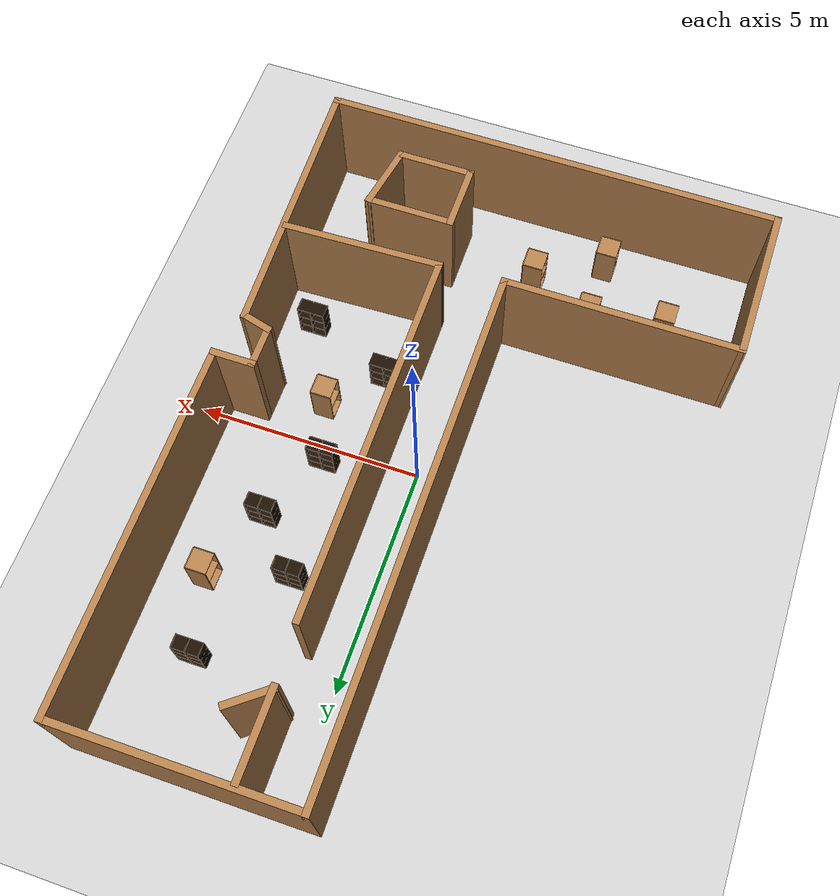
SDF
<sdf version="1.6">
 <world name="default">
  <light name="sun" type="directional">
   <pose>0 0 10 0 -0 0</pose>
   <diffuse>0.8 0.8 0.8 1</diffuse>
   <specular>0.2 0.2 0.2 1</specular>
   <attenuation>
    <range>1000</range>
    <constant>0.9</constant>
    <linear>0.01</linear>
    <quadratic>0.001</quadratic>
   </attenuation>
   <direction>-0.5 0.1 -0.9</direction>
  </light>
  <model name="ground_plane">
   <static>1</static>
   <link name="link">
    <collision name="collision">
     <geometry><plane><normal>0 0 1</normal><size>100 100</size></plane></geometry>
     <surface><friction><ode><mu>100</mu><mu2>50</mu2></ode></friction></surface>
    </collision>
    <visual name="visual">
     <cast_shadows>0</cast_shadows>
     <geometry><plane><normal>0 0 1</normal><size>100 100</size></plane></geometry>
     <material>
      <script><uri>file://media/materials/scripts/gazebo.material</uri><name>Gazebo/Grey</name></script>
     </material>
    </visual>
   </link>
  </model>
  <gravity>0 0 -9.8</gravity>
  <magnetic_field>6e-06 2.3e-05 -4.2e-05</magnetic_field>
  <atmosphere type="adiabatic"/>
  <physics name="default_physics" default="0" type="ode">
   <max_step_size>0.001</max_step_size>
   <real_time_factor>1</real_time_factor>
   <real_time_update_rate>1000</real_time_update_rate>
  </physics>
  <scene><ambient>0.4 0.4 0.4 1</ambient><background>0.7 0.7 0.7 1</background><shadows>1</shadows></scene>
  <spherical_coordinates>
   <surface_model>EARTH_WGS84</surface_model>
   <latitude_deg>0</latitude_deg>
   <longitude_deg>0</longitude_deg>
   <elevation>0</elevation>
   <heading_deg>0</heading_deg>
  </spherical_coordinates>
  <model name="map_25">
   <link name="Wall_0">
    <pose>-0.05 -7.34892 0 0 -0 3.14159</pose>
    <visual name="Wall_0_Visual">
     <pose>0 0 1.25 0 -0 0</pose>
     <geometry><box><size>10.25 0.15 2.5</size></box></geometry>
     <material>
      <script><uri>file://media/materials/scripts/gazebo.material</uri><name>Gazebo/Wood</name></script>
      <ambient>1 1 1 1</ambient>
      <shader type="pixel"/>
     </material>
     <meta><layer>0</layer></meta>
    </visual>
    <collision name="Wall_0_Collision">
     <pose>0 0 1.25 0 -0 0</pose>
     <geometry><box><size>10.25 0.15 2.5</size></box></geometry>
     <surface>
      <friction>
       <ode><mu>1</mu><mu2>1</mu2><fdir1>0 0 0</fdir1><slip1>0</slip1><slip2>0</slip2></ode>
       <torsional>
        <coefficient>1</coefficient>
        <patch_radius>0</patch_radius>
        <surface_radius>0</surface_radius>
        <use_patch_radius>1</use_patch_radius>
        <ode><slip>0</slip></ode>
       </torsional>
      </friction>
      <bounce><restitution_coefficient>0</restitution_coefficient><threshold>1e+06</threshold></bounce>
      <contact>
       <collide_without_contact>0</collide_without_contact>
       <collide_without_contact_bitmask>1</collide_without_contact_bitmask>
       <collide_bitmask>1</collide_bitmask>
       <ode>
        <soft_cfm>0</soft_cfm>
        <soft_erp>0.2</soft_erp>
        <kp>1e+13</kp>
        <kd>1</kd>
        <max_vel>0.01</max_vel>
        <min_depth>0</min_depth>
       </ode>
       <bullet>
        <split_impulse>1</split_impulse>
        <split_impulse_penetration_threshold>-0.01</split_impulse_penetration_threshold>
        <soft_cfm>0</soft_cfm>
        <soft_erp>0.2</soft_erp>
        <kp>1e+13</kp>
        <kd>1</kd>
       </bullet>
      </contact>
     </surface>
    </collision>
   </link>
   <link name="Wall_1">
    <pose>-5.1 -5.67392 0 0 -0 1.5708</pose>
    <visual name="Wall_1_Visual">
     <pose>0 0 1.25 0 -0 0</pose>
     <geometry><box><size>3.5 0.15 2.5</size></box></geometry>
     <material>
      <script><uri>file://media/materials/scripts/gazebo.material</uri><name>Gazebo/Wood</name></script>
      <ambient>1 1 1 1</ambient>
      <shader type="pixel"/>
     </material>
     <meta><layer>0</layer></meta>
    </visual>
    <collision name="Wall_1_Collision">
     <pose>0 0 1.25 0 -0 0</pose>
     <geometry><box><size>3.5 0.15 2.5</size></box></geometry>
     <surface>
      <friction>
       <ode><mu>1</mu><mu2>1</mu2><fdir1>0 0 0</fdir1><slip1>0</slip1><slip2>0</slip2></ode>
       <torsional>
        <coefficient>1</coefficient>
        <patch_radius>0</patch_radius>
        <surface_radius>0</surface_radius>
        <use_patch_radius>1</use_patch_radius>
        <ode><slip>0</slip></ode>
       </torsional>
      </friction>
      <bounce><restitution_coefficient>0</restitution_coefficient><threshold>1e+06</threshold></bounce>
      <contact>
       <collide_without_contact>0</collide_without_contact>
       <collide_without_contact_bitmask>1</collide_without_contact_bitmask>
       <collide_bitmask>1</collide_bitmask>
       <ode>
        <soft_cfm>0</soft_cfm>
        <soft_erp>0.2</soft_erp>
        <kp>1e+13</kp>
        <kd>1</kd>
        <max_vel>0.01</max_vel>
        <min_depth>0</min_depth>
       </ode>
       <bullet>
        <split_impulse>1</split_impulse>
        <split_impulse_penetration_threshold>-0.01</split_impulse_penetration_threshold>
        <soft_cfm>0</soft_cfm>
        <soft_erp>0.2</soft_erp>
        <kp>1e+13</kp>
        <kd>1</kd>
       </bullet>
      </contact>
     </surface>
    </collision>
   </link>
   <link name="Wall_14">
    <pose>1.41533 0.157617 0 0 0 -1.5708</pose>
    <visual name="Wall_14_Visual">
     <pose>0 0 1.25 0 -0 0</pose>
     <geometry><box><size>8.25 0.15 2.5</size></box></geometry>
     <material>
      <script><uri>file://media/materials/scripts/gazebo.material</uri><name>Gazebo/Wood</name></script>
      <ambient>1 1 1 1</ambient>
      <shader type="pixel"/>
     </material>
     <meta><layer>0</layer></meta>
    </visual>
    <collision name="Wall_14_Collision">
     <pose>0 0 1.25 0 -0 0</pose>
     <geometry><box><size>8.25 0.15 2.5</size></box></geometry>
     <surface>
      <friction>
       <ode><mu>1</mu><mu2>1</mu2><fdir1>0 0 0</fdir1><slip1>0</slip1><slip2>0</slip2></ode>
       <torsional>
        <coefficient>1</coefficient>
        <patch_radius>0</patch_radius>
        <surface_radius>0</surface_radius>
        <use_patch_radius>1</use_patch_radius>
        <ode><slip>0</slip></ode>
       </torsional>
      </friction>
      <bounce><restitution_coefficient>0</restitution_coefficient><threshold>1e+06</threshold></bounce>
      <contact>
       <collide_without_contact>0</collide_without_contact>
       <collide_without_contact_bitmask>1</collide_without_contact_bitmask>
       <collide_bitmask>1</collide_bitmask>
       <ode>
        <soft_cfm>0</soft_cfm>
        <soft_erp>0.2</soft_erp>
        <kp>1e+13</kp>
        <kd>1</kd>
        <max_vel>0.01</max_vel>
        <min_depth>0</min_depth>
       </ode>
       <bullet>
        <split_impulse>1</split_impulse>
        <split_impulse_penetration_threshold>-0.01</split_impulse_penetration_threshold>
        <soft_cfm>0</soft_cfm>
        <soft_erp>0.2</soft_erp>
        <kp>1e+13</kp>
        <kd>1</kd>
       </bullet>
      </contact>
     </surface>
    </collision>
   </link>
   <link name="Wall_15">
    <pose>3.12632 -3.89238 0 0 -0 0.03126</pose>
    <visual name="Wall_15_Visual">
     <pose>0 0 1.25 0 -0 0</pose>
     <geometry><box><size>3.57365 0.15 2.5</size></box></geometry>
     <material>
      <script><uri>file://media/materials/scripts/gazebo.material</uri><name>Gazebo/Wood</name></script>
      <ambient>1 1 1 1</ambient>
      <shader type="pixel"/>
     </material>
     <meta><layer>0</layer></meta>
    </visual>
    <collision name="Wall_15_Collision">
     <pose>0 0 1.25 0 -0 0</pose>
     <geometry><box><size>3.57365 0.15 2.5</size></box></geometry>
     <surface>
      <friction>
       <ode><mu>1</mu><mu2>1</mu2><fdir1>0 0 0</fdir1><slip1>0</slip1><slip2>0</slip2></ode>
       <torsional>
        <coefficient>1</coefficient>
        <patch_radius>0</patch_radius>
        <surface_radius>0</surface_radius>
        <use_patch_radius>1</use_patch_radius>
        <ode><slip>0</slip></ode>
       </torsional>
      </friction>
      <bounce><restitution_coefficient>0</restitution_coefficient><threshold>1e+06</threshold></bounce>
      <contact>
       <collide_without_contact>0</collide_without_contact>
       <collide_without_contact_bitmask>1</collide_without_contact_bitmask>
       <collide_bitmask>1</collide_bitmask>
       <ode>
        <soft_cfm>0</soft_cfm>
        <soft_erp>0.2</soft_erp>
        <kp>1e+13</kp>
        <kd>1</kd>
        <max_vel>0.01</max_vel>
        <min_depth>0</min_depth>
       </ode>
       <bullet>
        <split_impulse>1</split_impulse>
        <split_impulse_penetration_threshold>-0.01</split_impulse_penetration_threshold>
        <soft_cfm>0</soft_cfm>
        <soft_erp>0.2</soft_erp>
        <kp>1e+13</kp>
        <kd>1</kd>
       </bullet>
      </contact>
     </surface>
    </collision>
   </link>
   <link name="Wall_2">
    <pose>-2.55 -3.99892 0 0 -0 0</pose>
    <visual name="Wall_2_Visual">
     <pose>0 0 1.25 0 -0 0</pose>
     <geometry><box><size>5.25 0.15 2.5</size></box></geometry>
     <material>
      <script><uri>file://media/materials/scripts/gazebo.material</uri><name>Gazebo/Wood</name></script>
      <ambient>1 1 1 1</ambient>
      <shader type="pixel"/>
     </material>
     <meta><layer>0</layer></meta>
    </visual>
    <collision name="Wall_2_Collision">
     <pose>0 0 1.25 0 -0 0</pose>
     <geometry><box><size>5.25 0.15 2.5</size></box></geometry>
     <surface>
      <friction>
       <ode><mu>1</mu><mu2>1</mu2><fdir1>0 0 0</fdir1><slip1>0</slip1><slip2>0</slip2></ode>
       <torsional>
        <coefficient>1</coefficient>
        <patch_radius>0</patch_radius>
        <surface_radius>0</surface_radius>
        <use_patch_radius>1</use_patch_radius>
        <ode><slip>0</slip></ode>
       </torsional>
      </friction>
      <bounce><restitution_coefficient>0</restitution_coefficient><threshold>1e+06</threshold></bounce>
      <contact>
       <collide_without_contact>0</collide_without_contact>
       <collide_without_contact_bitmask>1</collide_without_contact_bitmask>
       <collide_bitmask>1</collide_bitmask>
       <ode>
        <soft_cfm>0</soft_cfm>
        <soft_erp>0.2</soft_erp>
        <kp>1e+13</kp>
        <kd>1</kd>
        <max_vel>0.01</max_vel>
        <min_depth>0</min_depth>
       </ode>
       <bullet>
        <split_impulse>1</split_impulse>
        <split_impulse_penetration_threshold>-0.01</split_impulse_penetration_threshold>
        <soft_cfm>0</soft_cfm>
        <soft_erp>0.2</soft_erp>
        <kp>1e+13</kp>
        <kd>1</kd>
       </bullet>
      </contact>
     </surface>
    </collision>
   </link>
   <link name="Wall_29">
    <pose>1.35601 6.37111 0 0 0 -1.5708</pose>
    <visual name="Wall_29_Visual">
     <pose>0 0 1.25 0 -0 0</pose>
     <geometry><box><size>1.92214 0.15 2.5</size></box></geometry>
     <material>
      <script><uri>file://media/materials/scripts/gazebo.material</uri><name>Gazebo/Wood</name></script>
      <ambient>1 1 1 1</ambient>
      <shader type="pixel"/>
     </material>
     <meta><layer>0</layer></meta>
    </visual>
    <collision name="Wall_29_Collision">
     <pose>0 0 1.25 0 -0 0</pose>
     <geometry><box><size>1.92214 0.15 2.5</size></box></geometry>
     <surface>
      <friction>
       <ode><mu>1</mu><mu2>1</mu2><fdir1>0 0 0</fdir1><slip1>0</slip1><slip2>0</slip2></ode>
       <torsional>
        <coefficient>1</coefficient>
        <patch_radius>0</patch_radius>
        <surface_radius>0</surface_radius>
        <use_patch_radius>1</use_patch_radius>
        <ode><slip>0</slip></ode>
       </torsional>
      </friction>
      <bounce><restitution_coefficient>0</restitution_coefficient><threshold>1e+06</threshold></bounce>
      <contact>
       <collide_without_contact>0</collide_without_contact>
       <collide_without_contact_bitmask>1</collide_without_contact_bitmask>
       <collide_bitmask>1</collide_bitmask>
       <ode>
        <soft_cfm>0</soft_cfm>
        <soft_erp>0.2</soft_erp>
        <kp>1e+13</kp>
        <kd>1</kd>
        <max_vel>0.01</max_vel>
        <min_depth>0</min_depth>
       </ode>
       <bullet>
        <split_impulse>1</split_impulse>
        <split_impulse_penetration_threshold>-0.01</split_impulse_penetration_threshold>
        <soft_cfm>0</soft_cfm>
        <soft_erp>0.2</soft_erp>
        <kp>1e+13</kp>
        <kd>1</kd>
       </bullet>
      </contact>
     </surface>
    </collision>
   </link>
   <link name="Wall_3">
    <pose>0 1.67608 0 0 -0 1.5708</pose>
    <visual name="Wall_3_Visual">
     <pose>0 0 1.25 0 -0 0</pose>
     <geometry><box><size>11.5 0.15 2.5</size></box></geometry>
     <material>
      <script><uri>file://media/materials/scripts/gazebo.material</uri><name>Gazebo/Wood</name></script>
      <ambient>1 1 1 1</ambient>
      <shader type="pixel"/>
     </material>
     <meta><layer>0</layer></meta>
    </visual>
    <collision name="Wall_3_Collision">
     <pose>0 0 1.25 0 -0 0</pose>
     <geometry><box><size>11.5 0.15 2.5</size></box></geometry>
     <surface>
      <friction>
       <ode><mu>1</mu><mu2>1</mu2><fdir1>0 0 0</fdir1><slip1>0</slip1><slip2>0</slip2></ode>
       <torsional>
        <coefficient>1</coefficient>
        <patch_radius>0</patch_radius>
        <surface_radius>0</surface_radius>
        <use_patch_radius>1</use_patch_radius>
        <ode><slip>0</slip></ode>
       </torsional>
      </friction>
      <bounce><restitution_coefficient>0</restitution_coefficient><threshold>1e+06</threshold></bounce>
      <contact>
       <collide_without_contact>0</collide_without_contact>
       <collide_without_contact_bitmask>1</collide_without_contact_bitmask>
       <collide_bitmask>1</collide_bitmask>
       <ode>
        <soft_cfm>0</soft_cfm>
        <soft_erp>0.2</soft_erp>
        <kp>1e+13</kp>
        <kd>1</kd>
        <max_vel>0.01</max_vel>
        <min_depth>0</min_depth>
       </ode>
       <bullet>
        <split_impulse>1</split_impulse>
        <split_impulse_penetration_threshold>-0.01</split_impulse_penetration_threshold>
        <soft_cfm>0</soft_cfm>
        <soft_erp>0.2</soft_erp>
        <kp>1e+13</kp>
        <kd>1</kd>
       </bullet>
      </contact>
     </surface>
    </collision>
   </link>
   <link name="Wall_30">
    <pose>1.72407 5.80307 0 0 -0 0.655241</pose>
    <visual name="Wall_30_Visual">
     <pose>0 0 1.25 0 -0 0</pose>
     <geometry><box><size>1.07839 0.15 2.5</size></box></geometry>
     <material>
      <script><uri>file://media/materials/scripts/gazebo.material</uri><name>Gazebo/Wood</name></script>
      <ambient>1 1 1 1</ambient>
      <shader type="pixel"/>
     </material>
     <meta><layer>0</layer></meta>
    </visual>
    <collision name="Wall_30_Collision">
     <pose>0 0 1.25 0 -0 0</pose>
     <geometry><box><size>1.07839 0.15 2.5</size></box></geometry>
     <surface>
      <friction>
       <ode><mu>1</mu><mu2>1</mu2><fdir1>0 0 0</fdir1><slip1>0</slip1><slip2>0</slip2></ode>
       <torsional>
        <coefficient>1</coefficient>
        <patch_radius>0</patch_radius>
        <surface_radius>0</surface_radius>
        <use_patch_radius>1</use_patch_radius>
        <ode><slip>0</slip></ode>
       </torsional>
      </friction>
      <bounce><restitution_coefficient>0</restitution_coefficient><threshold>1e+06</threshold></bounce>
      <contact>
       <collide_without_contact>0</collide_without_contact>
       <collide_without_contact_bitmask>1</collide_without_contact_bitmask>
       <collide_bitmask>1</collide_bitmask>
       <ode>
        <soft_cfm>0</soft_cfm>
        <soft_erp>0.2</soft_erp>
        <kp>1e+13</kp>
        <kd>1</kd>
        <max_vel>0.01</max_vel>
        <min_depth>0</min_depth>
       </ode>
       <bullet>
        <split_impulse>1</split_impulse>
        <split_impulse_penetration_threshold>-0.01</split_impulse_penetration_threshold>
        <soft_cfm>0</soft_cfm>
        <soft_erp>0.2</soft_erp>
        <kp>1e+13</kp>
        <kd>1</kd>
       </bullet>
      </contact>
     </surface>
    </collision>
   </link>
   <link name="Wall_32">
    <pose>2.46009 -5.04355 0 0 -0 3.14159</pose>
    <visual name="Wall_32_Visual">
     <pose>0 0 1.25 0 -0 0</pose>
     <geometry><box><size>2 0.15 2.5</size></box></geometry>
     <material>
      <script><uri>file://media/materials/scripts/gazebo.material</uri><name>Gazebo/Wood</name></script>
      <ambient>1 1 1 1</ambient>
      <shader type="pixel"/>
     </material>
     <meta><layer>0</layer></meta>
    </visual>
    <collision name="Wall_32_Collision">
     <pose>0 0 1.25 0 -0 0</pose>
     <geometry><box><size>2 0.15 2.5</size></box></geometry>
     <surface>
      <friction>
       <ode><mu>1</mu><mu2>1</mu2><fdir1>0 0 0</fdir1><slip1>0</slip1><slip2>0</slip2></ode>
       <torsional>
        <coefficient>1</coefficient>
        <patch_radius>0</patch_radius>
        <surface_radius>0</surface_radius>
        <use_patch_radius>1</use_patch_radius>
        <ode><slip>0</slip></ode>
       </torsional>
      </friction>
      <bounce><restitution_coefficient>0</restitution_coefficient><threshold>1e+06</threshold></bounce>
      <contact>
       <collide_without_contact>0</collide_without_contact>
       <collide_without_contact_bitmask>1</collide_without_contact_bitmask>
       <collide_bitmask>1</collide_bitmask>
       <ode>
        <soft_cfm>0</soft_cfm>
        <soft_erp>0.2</soft_erp>
        <kp>1e+13</kp>
        <kd>1</kd>
        <max_vel>0.01</max_vel>
        <min_depth>0</min_depth>
       </ode>
       <bullet>
        <split_impulse>1</split_impulse>
        <split_impulse_penetration_threshold>-0.01</split_impulse_penetration_threshold>
        <soft_cfm>0</soft_cfm>
        <soft_erp>0.2</soft_erp>
        <kp>1e+13</kp>
        <kd>1</kd>
       </bullet>
      </contact>
     </surface>
    </collision>
   </link>
   <link name="Wall_33">
    <pose>1.53509 -5.71855 0 0 0 -1.5708</pose>
    <visual name="Wall_33_Visual">
     <pose>0 0 1.25 0 -0 0</pose>
     <geometry><box><size>1.5 0.15 2.5</size></box></geometry>
     <material>
      <script><uri>file://media/materials/scripts/gazebo.material</uri><name>Gazebo/Wood</name></script>
      <ambient>1 1 1 1</ambient>
      <shader type="pixel"/>
     </material>
     <meta><layer>0</layer></meta>
    </visual>
    <collision name="Wall_33_Collision">
     <pose>0 0 1.25 0 -0 0</pose>
     <geometry><box><size>1.5 0.15 2.5</size></box></geometry>
     <surface>
      <friction>
       <ode><mu>1</mu><mu2>1</mu2><fdir1>0 0 0</fdir1><slip1>0</slip1><slip2>0</slip2></ode>
       <torsional>
        <coefficient>1</coefficient>
        <patch_radius>0</patch_radius>
        <surface_radius>0</surface_radius>
        <use_patch_radius>1</use_patch_radius>
        <ode><slip>0</slip></ode>
       </torsional>
      </friction>
      <bounce><restitution_coefficient>0</restitution_coefficient><threshold>1e+06</threshold></bounce>
      <contact>
       <collide_without_contact>0</collide_without_contact>
       <collide_without_contact_bitmask>1</collide_without_contact_bitmask>
       <collide_bitmask>1</collide_bitmask>
       <ode>
        <soft_cfm>0</soft_cfm>
        <soft_erp>0.2</soft_erp>
        <kp>1e+13</kp>
        <kd>1</kd>
        <max_vel>0.01</max_vel>
        <min_depth>0</min_depth>
       </ode>
       <bullet>
        <split_impulse>1</split_impulse>
        <split_impulse_penetration_threshold>-0.01</split_impulse_penetration_threshold>
        <soft_cfm>0</soft_cfm>
        <soft_erp>0.2</soft_erp>
        <kp>1e+13</kp>
        <kd>1</kd>
       </bullet>
      </contact>
     </surface>
    </collision>
   </link>
   <link name="Wall_34">
    <pose>2.33509 -6.39355 0 0 -0 0</pose>
    <visual name="Wall_34_Visual">
     <pose>0 0 1.25 0 -0 0</pose>
     <geometry><box><size>1.75 0.15 2.5</size></box></geometry>
     <material>
      <script><uri>file://media/materials/scripts/gazebo.material</uri><name>Gazebo/Wood</name></script>
      <ambient>1 1 1 1</ambient>
      <shader type="pixel"/>
     </material>
     <meta><layer>0</layer></meta>
    </visual>
    <collision name="Wall_34_Collision">
     <pose>0 0 1.25 0 -0 0</pose>
     <geometry><box><size>1.75 0.15 2.5</size></box></geometry>
     <surface>
      <friction>
       <ode><mu>1</mu><mu2>1</mu2><fdir1>0 0 0</fdir1><slip1>0</slip1><slip2>0</slip2></ode>
       <torsional>
        <coefficient>1</coefficient>
        <patch_radius>0</patch_radius>
        <surface_radius>0</surface_radius>
        <use_patch_radius>1</use_patch_radius>
        <ode><slip>0</slip></ode>
       </torsional>
      </friction>
      <bounce><restitution_coefficient>0</restitution_coefficient><threshold>1e+06</threshold></bounce>
      <contact>
       <collide_without_contact>0</collide_without_contact>
       <collide_without_contact_bitmask>1</collide_without_contact_bitmask>
       <collide_bitmask>1</collide_bitmask>
       <ode>
        <soft_cfm>0</soft_cfm>
        <soft_erp>0.2</soft_erp>
        <kp>1e+13</kp>
        <kd>1</kd>
        <max_vel>0.01</max_vel>
        <min_depth>0</min_depth>
       </ode>
       <bullet>
        <split_impulse>1</split_impulse>
        <split_impulse_penetration_threshold>-0.01</split_impulse_penetration_threshold>
        <soft_cfm>0</soft_cfm>
        <soft_erp>0.2</soft_erp>
        <kp>1e+13</kp>
        <kd>1</kd>
       </bullet>
      </contact>
     </surface>
    </collision>
   </link>
   <link name="Wall_35">
    <pose>3.26009 -5.71855 0 0 -0 1.38769</pose>
    <visual name="Wall_35_Visual">
     <pose>0 0 1.25 0 -0 0</pose>
     <geometry><box><size>1.52295 0.15 2.5</size></box></geometry>
     <material>
      <script><uri>file://media/materials/scripts/gazebo.material</uri><name>Gazebo/Wood</name></script>
      <ambient>1 1 1 1</ambient>
      <shader type="pixel"/>
     </material>
     <meta><layer>0</layer></meta>
    </visual>
    <collision name="Wall_35_Collision">
     <pose>0 0 1.25 0 -0 0</pose>
     <geometry><box><size>1.52295 0.15 2.5</size></box></geometry>
     <surface>
      <friction>
       <ode><mu>1</mu><mu2>1</mu2><fdir1>0 0 0</fdir1><slip1>0</slip1><slip2>0</slip2></ode>
       <torsional>
        <coefficient>1</coefficient>
        <patch_radius>0</patch_radius>
        <surface_radius>0</surface_radius>
        <use_patch_radius>1</use_patch_radius>
        <ode><slip>0</slip></ode>
       </torsional>
      </friction>
      <bounce><restitution_coefficient>0</restitution_coefficient><threshold>1e+06</threshold></bounce>
      <contact>
       <collide_without_contact>0</collide_without_contact>
       <collide_without_contact_bitmask>1</collide_without_contact_bitmask>
       <collide_bitmask>1</collide_bitmask>
       <ode>
        <soft_cfm>0</soft_cfm>
        <soft_erp>0.2</soft_erp>
        <kp>1e+13</kp>
        <kd>1</kd>
        <max_vel>0.01</max_vel>
        <min_depth>0</min_depth>
       </ode>
       <bullet>
        <split_impulse>1</split_impulse>
        <split_impulse_penetration_threshold>-0.01</split_impulse_penetration_threshold>
        <soft_cfm>0</soft_cfm>
        <soft_erp>0.2</soft_erp>
        <kp>1e+13</kp>
        <kd>1</kd>
       </bullet>
      </contact>
     </surface>
    </collision>
   </link>
   <link name="Wall_4">
    <pose>2.55 7.35108 0 0 -0 0</pose>
    <visual name="Wall_4_Visual">
     <pose>0 0 1.25 0 -0 0</pose>
     <geometry><box><size>5.25 0.15 2.5</size></box></geometry>
     <material>
      <script><uri>file://media/materials/scripts/gazebo.material</uri><name>Gazebo/Wood</name></script>
      <ambient>1 1 1 1</ambient>
      <shader type="pixel"/>
     </material>
     <meta><layer>0</layer></meta>
    </visual>
    <collision name="Wall_4_Collision">
     <pose>0 0 1.25 0 -0 0</pose>
     <geometry><box><size>5.25 0.15 2.5</size></box></geometry>
     <surface>
      <friction>
       <ode><mu>1</mu><mu2>1</mu2><fdir1>0 0 0</fdir1><slip1>0</slip1><slip2>0</slip2></ode>
       <torsional>
        <coefficient>1</coefficient>
        <patch_radius>0</patch_radius>
        <surface_radius>0</surface_radius>
        <use_patch_radius>1</use_patch_radius>
        <ode><slip>0</slip></ode>
       </torsional>
      </friction>
      <bounce><restitution_coefficient>0</restitution_coefficient><threshold>1e+06</threshold></bounce>
      <contact>
       <collide_without_contact>0</collide_without_contact>
       <collide_without_contact_bitmask>1</collide_without_contact_bitmask>
       <collide_bitmask>1</collide_bitmask>
       <ode>
        <soft_cfm>0</soft_cfm>
        <soft_erp>0.2</soft_erp>
        <kp>1e+13</kp>
        <kd>1</kd>
        <max_vel>0.01</max_vel>
        <min_depth>0</min_depth>
       </ode>
       <bullet>
        <split_impulse>1</split_impulse>
        <split_impulse_penetration_threshold>-0.01</split_impulse_penetration_threshold>
        <soft_cfm>0</soft_cfm>
        <soft_erp>0.2</soft_erp>
        <kp>1e+13</kp>
        <kd>1</kd>
       </bullet>
      </contact>
     </surface>
    </collision>
   </link>
   <link name="Wall_5">
    <pose>5.1 3.42608 0 0 0 -1.5708</pose>
    <visual name="Wall_5_Visual">
     <pose>0 0 1.25 0 -0 0</pose>
     <geometry><box><size>8 0.15 2.5</size></box></geometry>
     <material>
      <script><uri>file://media/materials/scripts/gazebo.material</uri><name>Gazebo/Wood</name></script>
      <ambient>1 1 1 1</ambient>
      <shader type="pixel"/>
     </material>
     <meta><layer>0</layer></meta>
    </visual>
    <collision name="Wall_5_Collision">
     <pose>0 0 1.25 0 -0 0</pose>
     <geometry><box><size>8 0.15 2.5</size></box></geometry>
     <surface>
      <friction>
       <ode><mu>1</mu><mu2>1</mu2><fdir1>0 0 0</fdir1><slip1>0</slip1><slip2>0</slip2></ode>
       <torsional>
        <coefficient>1</coefficient>
        <patch_radius>0</patch_radius>
        <surface_radius>0</surface_radius>
        <use_patch_radius>1</use_patch_radius>
        <ode><slip>0</slip></ode>
       </torsional>
      </friction>
      <bounce><restitution_coefficient>0</restitution_coefficient><threshold>1e+06</threshold></bounce>
      <contact>
       <collide_without_contact>0</collide_without_contact>
       <collide_without_contact_bitmask>1</collide_without_contact_bitmask>
       <collide_bitmask>1</collide_bitmask>
       <ode>
        <soft_cfm>0</soft_cfm>
        <soft_erp>0.2</soft_erp>
        <kp>1e+13</kp>
        <kd>1</kd>
        <max_vel>0.01</max_vel>
        <min_depth>0</min_depth>
       </ode>
       <bullet>
        <split_impulse>1</split_impulse>
        <split_impulse_penetration_threshold>-0.01</split_impulse_penetration_threshold>
        <soft_cfm>0</soft_cfm>
        <soft_erp>0.2</soft_erp>
        <kp>1e+13</kp>
        <kd>1</kd>
       </bullet>
      </contact>
     </surface>
    </collision>
   </link>
   <link name="Wall_6">
    <pose>4.675 -0.498923 0 0 -0 3.14159</pose>
    <visual name="Wall_6_Visual">
     <pose>0 0 1.25 0 -0 0</pose>
     <geometry><box><size>1 0.15 2.5</size></box></geometry>
     <material>
      <script><uri>file://media/materials/scripts/gazebo.material</uri><name>Gazebo/Wood</name></script>
      <ambient>1 1 1 1</ambient>
      <shader type="pixel"/>
     </material>
     <meta><layer>0</layer></meta>
    </visual>
    <collision name="Wall_6_Collision">
     <pose>0 0 1.25 0 -0 0</pose>
     <geometry><box><size>1 0.15 2.5</size></box></geometry>
     <surface>
      <friction>
       <ode><mu>1</mu><mu2>1</mu2><fdir1>0 0 0</fdir1><slip1>0</slip1><slip2>0</slip2></ode>
       <torsional>
        <coefficient>1</coefficient>
        <patch_radius>0</patch_radius>
        <surface_radius>0</surface_radius>
        <use_patch_radius>1</use_patch_radius>
        <ode><slip>0</slip></ode>
       </torsional>
      </friction>
      <bounce><restitution_coefficient>0</restitution_coefficient><threshold>1e+06</threshold></bounce>
      <contact>
       <collide_without_contact>0</collide_without_contact>
       <collide_without_contact_bitmask>1</collide_without_contact_bitmask>
       <collide_bitmask>1</collide_bitmask>
       <ode>
        <soft_cfm>0</soft_cfm>
        <soft_erp>0.2</soft_erp>
        <kp>1e+13</kp>
        <kd>1</kd>
        <max_vel>0.01</max_vel>
        <min_depth>0</min_depth>
       </ode>
       <bullet>
        <split_impulse>1</split_impulse>
        <split_impulse_penetration_threshold>-0.01</split_impulse_penetration_threshold>
        <soft_cfm>0</soft_cfm>
        <soft_erp>0.2</soft_erp>
        <kp>1e+13</kp>
        <kd>1</kd>
       </bullet>
      </contact>
     </surface>
    </collision>
   </link>
   <link name="Wall_7">
    <pose>4.25 -0.923923 0 0 0 -1.5708</pose>
    <visual name="Wall_7_Visual">
     <pose>0 0 1.25 0 -0 0</pose>
     <geometry><box><size>1 0.15 2.5</size></box></geometry>
     <material>
      <script><uri>file://media/materials/scripts/gazebo.material</uri><name>Gazebo/Wood</name></script>
      <ambient>1 1 1 1</ambient>
      <shader type="pixel"/>
     </material>
     <meta><layer>0</layer></meta>
    </visual>
    <collision name="Wall_7_Collision">
     <pose>0 0 1.25 0 -0 0</pose>
     <geometry><box><size>1 0.15 2.5</size></box></geometry>
     <surface>
      <friction>
       <ode><mu>1</mu><mu2>1</mu2><fdir1>0 0 0</fdir1><slip1>0</slip1><slip2>0</slip2></ode>
       <torsional>
        <coefficient>1</coefficient>
        <patch_radius>0</patch_radius>
        <surface_radius>0</surface_radius>
        <use_patch_radius>1</use_patch_radius>
        <ode><slip>0</slip></ode>
       </torsional>
      </friction>
      <bounce><restitution_coefficient>0</restitution_coefficient><threshold>1e+06</threshold></bounce>
      <contact>
       <collide_without_contact>0</collide_without_contact>
       <collide_without_contact_bitmask>1</collide_without_contact_bitmask>
       <collide_bitmask>1</collide_bitmask>
       <ode>
        <soft_cfm>0</soft_cfm>
        <soft_erp>0.2</soft_erp>
        <kp>1e+13</kp>
        <kd>1</kd>
        <max_vel>0.01</max_vel>
        <min_depth>0</min_depth>
       </ode>
       <bullet>
        <split_impulse>1</split_impulse>
        <split_impulse_penetration_threshold>-0.01</split_impulse_penetration_threshold>
        <soft_cfm>0</soft_cfm>
        <soft_erp>0.2</soft_erp>
        <kp>1e+13</kp>
        <kd>1</kd>
       </bullet>
      </contact>
     </surface>
    </collision>
   </link>
   <link name="Wall_8">
    <pose>4.53978 -1.42657 0 0 0 -0.261799</pose>
    <visual name="Wall_8_Visual">
     <pose>0 0 1.25 0 -0 0</pose>
     <geometry><box><size>0.75 0.15 2.5</size></box></geometry>
     <material>
      <script><uri>file://media/materials/scripts/gazebo.material</uri><name>Gazebo/Wood</name></script>
      <ambient>1 1 1 1</ambient>
      <shader type="pixel"/>
     </material>
     <meta><layer>0</layer></meta>
    </visual>
    <collision name="Wall_8_Collision">
     <pose>0 0 1.25 0 -0 0</pose>
     <geometry><box><size>0.75 0.15 2.5</size></box></geometry>
     <surface>
      <friction>
       <ode><mu>1</mu><mu2>1</mu2><fdir1>0 0 0</fdir1><slip1>0</slip1><slip2>0</slip2></ode>
       <torsional>
        <coefficient>1</coefficient>
        <patch_radius>0</patch_radius>
        <surface_radius>0</surface_radius>
        <use_patch_radius>1</use_patch_radius>
        <ode><slip>0</slip></ode>
       </torsional>
      </friction>
      <bounce><restitution_coefficient>0</restitution_coefficient><threshold>1e+06</threshold></bounce>
      <contact>
       <collide_without_contact>0</collide_without_contact>
       <collide_without_contact_bitmask>1</collide_without_contact_bitmask>
       <collide_bitmask>1</collide_bitmask>
       <ode>
        <soft_cfm>0</soft_cfm>
        <soft_erp>0.2</soft_erp>
        <kp>1e+13</kp>
        <kd>1</kd>
        <max_vel>0.01</max_vel>
        <min_depth>0</min_depth>
       </ode>
       <bullet>
        <split_impulse>1</split_impulse>
        <split_impulse_penetration_threshold>-0.01</split_impulse_penetration_threshold>
        <soft_cfm>0</soft_cfm>
        <soft_erp>0.2</soft_erp>
        <kp>1e+13</kp>
        <kd>1</kd>
       </bullet>
      </contact>
     </surface>
    </collision>
   </link>
   <link name="Wall_9">
    <pose>4.91478 -4.42657 0 0 0 -1.54164</pose>
    <visual name="Wall_9_Visual">
     <pose>0 0 1.25 0 -0 0</pose>
     <geometry><box><size>5.99719 0.15 2.5</size></box></geometry>
     <material>
      <script><uri>file://media/materials/scripts/gazebo.material</uri><name>Gazebo/Wood</name></script>
      <ambient>1 1 1 1</ambient>
      <shader type="pixel"/>
     </material>
     <meta><layer>0</layer></meta>
    </visual>
    <collision name="Wall_9_Collision">
     <pose>0 0 1.25 0 -0 0</pose>
     <geometry><box><size>5.99719 0.15 2.5</size></box></geometry>
     <surface>
      <friction>
       <ode><mu>1</mu><mu2>1</mu2><fdir1>0 0 0</fdir1><slip1>0</slip1><slip2>0</slip2></ode>
       <torsional>
        <coefficient>1</coefficient>
        <patch_radius>0</patch_radius>
        <surface_radius>0</surface_radius>
        <use_patch_radius>1</use_patch_radius>
        <ode><slip>0</slip></ode>
       </torsional>
      </friction>
      <bounce><restitution_coefficient>0</restitution_coefficient><threshold>1e+06</threshold></bounce>
      <contact>
       <collide_without_contact>0</collide_without_contact>
       <collide_without_contact_bitmask>1</collide_without_contact_bitmask>
       <collide_bitmask>1</collide_bitmask>
       <ode>
        <soft_cfm>0</soft_cfm>
        <soft_erp>0.2</soft_erp>
        <kp>1e+13</kp>
        <kd>1</kd>
        <max_vel>0.01</max_vel>
        <min_depth>0</min_depth>
       </ode>
       <bullet>
        <split_impulse>1</split_impulse>
        <split_impulse_penetration_threshold>-0.01</split_impulse_penetration_threshold>
        <soft_cfm>0</soft_cfm>
        <soft_erp>0.2</soft_erp>
        <kp>1e+13</kp>
        <kd>1</kd>
       </bullet>
      </contact>
     </surface>
    </collision>
   </link>
   <static>1</static>
   <pose>-0.646899 0.20594 0 0 -0 0</pose>
  </model>
  <model name="6_Cube_StorageE">
   <link name="Wall_0">
    <pose>0 0 0.01 0 -0 0</pose>
    <inertial>
     <mass>1.6201</mass>
     <inertia><ixx>0.0119</ixx><iyy>0.0631</iyy><izz>0.0513</izz><ixy>0</ixy><ixz>0</ixz><iyz>0</iyz></inertia>
    </inertial>
    <collision name="Wall_0_Collision"><geometry><box><size>0.616 0.296 0.02</size></box></geometry></collision>
    <visual name="Wall_0_Visual">
     <geometry><box><size>0.616 0.296 0.02</size></box></geometry>
     <material>
      <script><uri>file://media/materials/scripts/gazebo.material</uri><name>Gazebo/Grey</name></script>
      <ambient>0.105882 0.0509804 0 1</ambient>
     </material>
    </visual>
   </link>
   <joint name="0_2" type="fixed">
    <pose>-0.308 0 0 0 -0 0</pose>
    <parent>Wall_2</parent>
    <child>Wall_0</child>
    <axis>
     <xyz>1 0 0</xyz>
     <use_parent_model_frame>0</use_parent_model_frame>
     <limit><lower>-1e+16</lower><upper>1e+16</upper></limit>
    </axis>
   </joint>
   <joint name="0_12" type="fixed">
    <parent>Wall_12</parent>
    <child>Wall_0</child>
    <axis>
     <xyz>0 0 1</xyz>
     <use_parent_model_frame>0</use_parent_model_frame>
     <limit><lower>-1e+16</lower><upper>1e+16</upper></limit>
    </axis>
   </joint>
   <joint name="0_4" type="fixed">
    <pose>0.308 0 0 0 -0 0</pose>
    <parent>Wall_4</parent>
    <child>Wall_0</child>
    <axis>
     <xyz>1 0 0</xyz>
     <use_parent_model_frame>0</use_parent_model_frame>
     <limit><lower>-1e+16</lower><upper>1e+16</upper></limit>
    </axis>
   </joint>
   <link name="Wall_10">
    <pose>0 0 0.61 0 -0 0</pose>
    <inertial>
     <mass>1.6201</mass>
     <inertia><ixx>0.0119</ixx><iyy>0.0631</iyy><izz>0.0513</izz><ixy>0</ixy><ixz>0</ixz><iyz>0</iyz></inertia>
    </inertial>
    <collision name="Wall_10_Collision"><geometry><box><size>0.616 0.296 0.02</size></box></geometry></collision>
    <visual name="Wall_10_Visual">
     <geometry><box><size>0.616 0.296 0.02</size></box></geometry>
     <material>
      <script><uri>file://media/materials/scripts/gazebo.material</uri><name>Gazebo/Grey</name></script>
      <ambient>0.105882 0.0509804 0 1</ambient>
     </material>
    </visual>
   </link>
   <joint name="10_2" type="fixed">
    <pose>-0.308 0 0 0 -0 0</pose>
    <parent>Wall_2</parent>
    <child>Wall_10</child>
    <axis>
     <xyz>1 0 0</xyz>
     <use_parent_model_frame>0</use_parent_model_frame>
     <limit><lower>-1e+16</lower><upper>1e+16</upper></limit>
    </axis>
   </joint>
   <joint name="10_12" type="fixed">
    <parent>Wall_12</parent>
    <child>Wall_10</child>
    <axis>
     <xyz>0 0 1</xyz>
     <use_parent_model_frame>0</use_parent_model_frame>
     <limit><lower>-1e+16</lower><upper>1e+16</upper></limit>
    </axis>
   </joint>
   <joint name="10_4" type="fixed">
    <pose>0.308 0 0 0 -0 0</pose>
    <parent>Wall_4</parent>
    <child>Wall_10</child>
    <axis>
     <xyz>1 0 0</xyz>
     <use_parent_model_frame>0</use_parent_model_frame>
     <limit><lower>-1e+16</lower><upper>1e+16</upper></limit>
    </axis>
   </joint>
   <link name="Wall_12">
    <pose>0 0 0.4575 0 -0 0</pose>
    <inertial>
     <mass>2.4065</mass>
     <inertia><ixx>0.0177</ixx><iyy>0.1855</iyy><izz>0.168</izz><ixy>0</ixy><ixz>0</ixz><iyz>0</iyz></inertia>
    </inertial>
    <collision name="Wall_12_Collision"><geometry><box><size>0.02 0.296 0.915</size></box></geometry></collision>
    <visual name="Wall_12_Visual">
     <geometry><box><size>0.02 0.296 0.915</size></box></geometry>
     <material>
      <script><uri>file://media/materials/scripts/gazebo.material</uri><name>Gazebo/Grey</name></script>
      <ambient>0.105882 0.0509804 0 1</ambient>
     </material>
    </visual>
   </link>
   <link name="Wall_2">
    <pose>-0.298 0 0.4575 0 -0 0</pose>
    <inertial>
     <mass>2.4065</mass>
     <inertia><ixx>0.0177</ixx><iyy>0.1855</iyy><izz>0.168</izz><ixy>0</ixy><ixz>0</ixz><iyz>0</iyz></inertia>
    </inertial>
    <collision name="Wall_2_Collision"><geometry><box><size>0.02 0.296 0.915</size></box></geometry></collision>
    <visual name="Wall_2_Visual">
     <geometry><box><size>0.02 0.296 0.915</size></box></geometry>
     <material>
      <script><uri>file://media/materials/scripts/gazebo.material</uri><name>Gazebo/Grey</name></script>
      <ambient>0.105882 0.0509804 0 1</ambient>
     </material>
    </visual>
   </link>
   <link name="Wall_4">
    <pose>0.298 0 0.4575 0 -0 0</pose>
    <inertial>
     <mass>2.4065</mass>
     <inertia><ixx>0.0177</ixx><iyy>0.1855</iyy><izz>0.168</izz><ixy>0</ixy><ixz>0</ixz><iyz>0</iyz></inertia>
    </inertial>
    <collision name="Wall_4_Collision"><geometry><box><size>0.02 0.296 0.915</size></box></geometry></collision>
    <visual name="Wall_4_Visual">
     <geometry><box><size>0.02 0.296 0.915</size></box></geometry>
     <material>
      <script><uri>file://media/materials/scripts/gazebo.material</uri><name>Gazebo/Grey</name></script>
      <ambient>0.105882 0.0509804 0 1</ambient>
     </material>
    </visual>
   </link>
   <link name="Wall_6">
    <pose>0 0 0.905 0 -0 0</pose>
    <inertial>
     <mass>1.6201</mass>
     <inertia><ixx>0.0119</ixx><iyy>0.0631</iyy><izz>0.0513</izz><ixy>0</ixy><ixz>0</ixz><iyz>0</iyz></inertia>
    </inertial>
    <collision name="Wall_6_Collision"><geometry><box><size>0.616 0.296 0.02</size></box></geometry></collision>
    <visual name="Wall_6_Visual">
     <geometry><box><size>0.616 0.296 0.02</size></box></geometry>
     <material>
      <script><uri>file://media/materials/scripts/gazebo.material</uri><name>Gazebo/Grey</name></script>
      <ambient>0.105882 0.0509804 0 1</ambient>
     </material>
    </visual>
   </link>
   <joint name="6_2" type="fixed">
    <pose>-0.308 0 0 0 -0 0</pose>
    <parent>Wall_2</parent>
    <child>Wall_6</child>
    <axis>
     <xyz>2 0 0</xyz>
     <use_parent_model_frame>0</use_parent_model_frame>
     <limit><lower>-1e+16</lower><upper>1e+16</upper></limit>
    </axis>
   </joint>
   <joint name="6_12" type="fixed">
    <parent>Wall_12</parent>
    <child>Wall_6</child>
    <axis>
     <xyz>0 0 1</xyz>
     <use_parent_model_frame>0</use_parent_model_frame>
     <limit><lower>-1e+16</lower><upper>1e+16</upper></limit>
    </axis>
   </joint>
   <joint name="6_4" type="fixed">
    <pose>0.308 0 0 0 -0 0</pose>
    <parent>Wall_4</parent>
    <child>Wall_6</child>
    <axis>
     <xyz>1 0 0</xyz>
     <use_parent_model_frame>0</use_parent_model_frame>
     <limit><lower>-1e+16</lower><upper>1e+16</upper></limit>
    </axis>
   </joint>
   <link name="Wall_8">
    <pose>0 0 0.305 0 -0 0</pose>
    <inertial>
     <mass>1.6201</mass>
     <inertia><ixx>0.0119</ixx><iyy>0.0631</iyy><izz>0.0513</izz><ixy>0</ixy><ixz>0</ixz><iyz>0</iyz></inertia>
    </inertial>
    <collision name="Wall_8_Collision"><geometry><box><size>0.616 0.296 0.02</size></box></geometry></collision>
    <visual name="Wall_8_Visual">
     <geometry><box><size>0.616 0.296 0.02</size></box></geometry>
     <material>
      <script><uri>file://media/materials/scripts/gazebo.material</uri><name>Gazebo/Grey</name></script>
      <ambient>0.105882 0.0509804 0 1</ambient>
     </material>
    </visual>
   </link>
   <joint name="8_2" type="fixed">
    <pose>-0.308 0 0 0 -0 0</pose>
    <parent>Wall_2</parent>
    <child>Wall_8</child>
    <axis>
     <xyz>1 0 0</xyz>
     <use_parent_model_frame>0</use_parent_model_frame>
     <limit><lower>-1e+16</lower><upper>1e+16</upper></limit>
    </axis>
   </joint>
   <joint name="8_12" type="fixed">
    <parent>Wall_12</parent>
    <child>Wall_8</child>
    <axis>
     <xyz>0 0 1</xyz>
     <use_parent_model_frame>0</use_parent_model_frame>
     <limit><lower>-1e+16</lower><upper>1e+16</upper></limit>
    </axis>
   </joint>
   <joint name="8_4" type="fixed">
    <pose>0.308 0 0 0 -0 0</pose>
    <parent>Wall_4</parent>
    <child>Wall_8</child>
    <axis>
     <xyz>1 0 0</xyz>
     <use_parent_model_frame>0</use_parent_model_frame>
     <limit><lower>-1e+16</lower><upper>1e+16</upper></limit>
    </axis>
   </joint>
   <static>1</static>
   <pose>1.70238 3.03871 0 0 -0 0</pose>
  </model>
  <model name="6_Cube_StorageE_0">
   <link name="Wall_0">
    <pose>0 0 0.01 0 -0 0</pose>
    <inertial>
     <mass>1.6201</mass>
     <inertia><ixx>0.0119</ixx><iyy>0.0631</iyy><izz>0.0513</izz><ixy>0</ixy><ixz>0</ixz><iyz>0</iyz></inertia>
    </inertial>
    <collision name="Wall_0_Collision"><geometry><box><size>0.616 0.296 0.02</size></box></geometry></collision>
    <visual name="Wall_0_Visual">
     <geometry><box><size>0.616 0.296 0.02</size></box></geometry>
     <material>
      <script><uri>file://media/materials/scripts/gazebo.material</uri><name>Gazebo/Grey</name></script>
      <ambient>0.105882 0.0509804 0 1</ambient>
     </material>
    </visual>
   </link>
   <joint name="0_2" type="fixed">
    <pose>-0.308 0 0 0 -0 0</pose>
    <parent>Wall_2</parent>
    <child>Wall_0</child>
    <axis>
     <xyz>1 0 0</xyz>
     <use_parent_model_frame>0</use_parent_model_frame>
     <limit><lower>-1e+16</lower><upper>1e+16</upper></limit>
    </axis>
   </joint>
   <joint name="0_12" type="fixed">
    <parent>Wall_12</parent>
    <child>Wall_0</child>
    <axis>
     <xyz>0 0 1</xyz>
     <use_parent_model_frame>0</use_parent_model_frame>
     <limit><lower>-1e+16</lower><upper>1e+16</upper></limit>
    </axis>
   </joint>
   <joint name="0_4" type="fixed">
    <pose>0.308 0 0 0 -0 0</pose>
    <parent>Wall_4</parent>
    <child>Wall_0</child>
    <axis>
     <xyz>1 0 0</xyz>
     <use_parent_model_frame>0</use_parent_model_frame>
     <limit><lower>-1e+16</lower><upper>1e+16</upper></limit>
    </axis>
   </joint>
   <link name="Wall_10">
    <pose>0 0 0.61 0 -0 0</pose>
    <inertial>
     <mass>1.6201</mass>
     <inertia><ixx>0.0119</ixx><iyy>0.0631</iyy><izz>0.0513</izz><ixy>0</ixy><ixz>0</ixz><iyz>0</iyz></inertia>
    </inertial>
    <collision name="Wall_10_Collision"><geometry><box><size>0.616 0.296 0.02</size></box></geometry></collision>
    <visual name="Wall_10_Visual">
     <geometry><box><size>0.616 0.296 0.02</size></box></geometry>
     <material>
      <script><uri>file://media/materials/scripts/gazebo.material</uri><name>Gazebo/Grey</name></script>
      <ambient>0.105882 0.0509804 0 1</ambient>
     </material>
    </visual>
   </link>
   <joint name="10_2" type="fixed">
    <pose>-0.308 0 0 0 -0 0</pose>
    <parent>Wall_2</parent>
    <child>Wall_10</child>
    <axis>
     <xyz>1 0 0</xyz>
     <use_parent_model_frame>0</use_parent_model_frame>
     <limit><lower>-1e+16</lower><upper>1e+16</upper></limit>
    </axis>
   </joint>
   <joint name="10_12" type="fixed">
    <parent>Wall_12</parent>
    <child>Wall_10</child>
    <axis>
     <xyz>0 0 1</xyz>
     <use_parent_model_frame>0</use_parent_model_frame>
     <limit><lower>-1e+16</lower><upper>1e+16</upper></limit>
    </axis>
   </joint>
   <joint name="10_4" type="fixed">
    <pose>0.308 0 0 0 -0 0</pose>
    <parent>Wall_4</parent>
    <child>Wall_10</child>
    <axis>
     <xyz>1 0 0</xyz>
     <use_parent_model_frame>0</use_parent_model_frame>
     <limit><lower>-1e+16</lower><upper>1e+16</upper></limit>
    </axis>
   </joint>
   <link name="Wall_12">
    <pose>0 0 0.4575 0 -0 0</pose>
    <inertial>
     <mass>2.4065</mass>
     <inertia><ixx>0.0177</ixx><iyy>0.1855</iyy><izz>0.168</izz><ixy>0</ixy><ixz>0</ixz><iyz>0</iyz></inertia>
    </inertial>
    <collision name="Wall_12_Collision"><geometry><box><size>0.02 0.296 0.915</size></box></geometry></collision>
    <visual name="Wall_12_Visual">
     <geometry><box><size>0.02 0.296 0.915</size></box></geometry>
     <material>
      <script><uri>file://media/materials/scripts/gazebo.material</uri><name>Gazebo/Grey</name></script>
      <ambient>0.105882 0.0509804 0 1</ambient>
     </material>
    </visual>
   </link>
   <link name="Wall_2">
    <pose>-0.298 0 0.4575 0 -0 0</pose>
    <inertial>
     <mass>2.4065</mass>
     <inertia><ixx>0.0177</ixx><iyy>0.1855</iyy><izz>0.168</izz><ixy>0</ixy><ixz>0</ixz><iyz>0</iyz></inertia>
    </inertial>
    <collision name="Wall_2_Collision"><geometry><box><size>0.02 0.296 0.915</size></box></geometry></collision>
    <visual name="Wall_2_Visual">
     <geometry><box><size>0.02 0.296 0.915</size></box></geometry>
     <material>
      <script><uri>file://media/materials/scripts/gazebo.material</uri><name>Gazebo/Grey</name></script>
      <ambient>0.105882 0.0509804 0 1</ambient>
     </material>
    </visual>
   </link>
   <link name="Wall_4">
    <pose>0.298 0 0.4575 0 -0 0</pose>
    <inertial>
     <mass>2.4065</mass>
     <inertia><ixx>0.0177</ixx><iyy>0.1855</iyy><izz>0.168</izz><ixy>0</ixy><ixz>0</ixz><iyz>0</iyz></inertia>
    </inertial>
    <collision name="Wall_4_Collision"><geometry><box><size>0.02 0.296 0.915</size></box></geometry></collision>
    <visual name="Wall_4_Visual">
     <geometry><box><size>0.02 0.296 0.915</size></box></geometry>
     <material>
      <script><uri>file://media/materials/scripts/gazebo.material</uri><name>Gazebo/Grey</name></script>
      <ambient>0.105882 0.0509804 0 1</ambient>
     </material>
    </visual>
   </link>
   <link name="Wall_6">
    <pose>0 0 0.905 0 -0 0</pose>
    <inertial>
     <mass>1.6201</mass>
     <inertia><ixx>0.0119</ixx><iyy>0.0631</iyy><izz>0.0513</izz><ixy>0</ixy><ixz>0</ixz><iyz>0</iyz></inertia>
    </inertial>
    <collision name="Wall_6_Collision"><geometry><box><size>0.616 0.296 0.02</size></box></geometry></collision>
    <visual name="Wall_6_Visual">
     <geometry><box><size>0.616 0.296 0.02</size></box></geometry>
     <material>
      <script><uri>file://media/materials/scripts/gazebo.material</uri><name>Gazebo/Grey</name></script>
      <ambient>0.105882 0.0509804 0 1</ambient>
     </material>
    </visual>
   </link>
   <joint name="6_2" type="fixed">
    <pose>-0.308 0 0 0 -0 0</pose>
    <parent>Wall_2</parent>
    <child>Wall_6</child>
    <axis>
     <xyz>2 0 0</xyz>
     <use_parent_model_frame>0</use_parent_model_frame>
     <limit><lower>-1e+16</lower><upper>1e+16</upper></limit>
    </axis>
   </joint>
   <joint name="6_12" type="fixed">
    <parent>Wall_12</parent>
    <child>Wall_6</child>
    <axis>
     <xyz>0 0 1</xyz>
     <use_parent_model_frame>0</use_parent_model_frame>
     <limit><lower>-1e+16</lower><upper>1e+16</upper></limit>
    </axis>
   </joint>
   <joint name="6_4" type="fixed">
    <pose>0.308 0 0 0 -0 0</pose>
    <parent>Wall_4</parent>
    <child>Wall_6</child>
    <axis>
     <xyz>1 0 0</xyz>
     <use_parent_model_frame>0</use_parent_model_frame>
     <limit><lower>-1e+16</lower><upper>1e+16</upper></limit>
    </axis>
   </joint>
   <link name="Wall_8">
    <pose>0 0 0.305 0 -0 0</pose>
    <inertial>
     <mass>1.6201</mass>
     <inertia><ixx>0.0119</ixx><iyy>0.0631</iyy><izz>0.0513</izz><ixy>0</ixy><ixz>0</ixz><iyz>0</iyz></inertia>
    </inertial>
    <collision name="Wall_8_Collision"><geometry><box><size>0.616 0.296 0.02</size></box></geometry></collision>
    <visual name="Wall_8_Visual">
     <geometry><box><size>0.616 0.296 0.02</size></box></geometry>
     <material>
      <script><uri>file://media/materials/scripts/gazebo.material</uri><name>Gazebo/Grey</name></script>
      <ambient>0.105882 0.0509804 0 1</ambient>
     </material>
    </visual>
   </link>
   <joint name="8_2" type="fixed">
    <pose>-0.308 0 0 0 -0 0</pose>
    <parent>Wall_2</parent>
    <child>Wall_8</child>
    <axis>
     <xyz>1 0 0</xyz>
     <use_parent_model_frame>0</use_parent_model_frame>
     <limit><lower>-1e+16</lower><upper>1e+16</upper></limit>
    </axis>
   </joint>
   <joint name="8_12" type="fixed">
    <parent>Wall_12</parent>
    <child>Wall_8</child>
    <axis>
     <xyz>0 0 1</xyz>
     <use_parent_model_frame>0</use_parent_model_frame>
     <limit><lower>-1e+16</lower><upper>1e+16</upper></limit>
    </axis>
   </joint>
   <joint name="8_4" type="fixed">
    <pose>0.308 0 0 0 -0 0</pose>
    <parent>Wall_4</parent>
    <child>Wall_8</child>
    <axis>
     <xyz>1 0 0</xyz>
     <use_parent_model_frame>0</use_parent_model_frame>
     <limit><lower>-1e+16</lower><upper>1e+16</upper></limit>
    </axis>
   </joint>
   <static>1</static>
   <pose>2.74991 1.93581 0 0 -0 0</pose>
  </model>
  <model name="6_Cube_StorageE_1">
   <link name="Wall_0">
    <pose>0 0 0.01 0 -0 0</pose>
    <inertial>
     <mass>1.6201</mass>
     <inertia><ixx>0.0119</ixx><iyy>0.0631</iyy><izz>0.0513</izz><ixy>0</ixy><ixz>0</ixz><iyz>0</iyz></inertia>
    </inertial>
    <collision name="Wall_0_Collision"><geometry><box><size>0.616 0.296 0.02</size></box></geometry></collision>
    <visual name="Wall_0_Visual">
     <geometry><box><size>0.616 0.296 0.02</size></box></geometry>
     <material>
      <script><uri>file://media/materials/scripts/gazebo.material</uri><name>Gazebo/Grey</name></script>
      <ambient>0.105882 0.0509804 0 1</ambient>
     </material>
    </visual>
   </link>
   <joint name="0_2" type="fixed">
    <pose>-0.308 0 0 0 -0 0</pose>
    <parent>Wall_2</parent>
    <child>Wall_0</child>
    <axis>
     <xyz>1 0 0</xyz>
     <use_parent_model_frame>0</use_parent_model_frame>
     <limit><lower>-1e+16</lower><upper>1e+16</upper></limit>
    </axis>
   </joint>
   <joint name="0_12" type="fixed">
    <parent>Wall_12</parent>
    <child>Wall_0</child>
    <axis>
     <xyz>0 0 1</xyz>
     <use_parent_model_frame>0</use_parent_model_frame>
     <limit><lower>-1e+16</lower><upper>1e+16</upper></limit>
    </axis>
   </joint>
   <joint name="0_4" type="fixed">
    <pose>0.308 0 0 0 -0 0</pose>
    <parent>Wall_4</parent>
    <child>Wall_0</child>
    <axis>
     <xyz>1 0 0</xyz>
     <use_parent_model_frame>0</use_parent_model_frame>
     <limit><lower>-1e+16</lower><upper>1e+16</upper></limit>
    </axis>
   </joint>
   <link name="Wall_10">
    <pose>0 0 0.61 0 -0 0</pose>
    <inertial>
     <mass>1.6201</mass>
     <inertia><ixx>0.0119</ixx><iyy>0.0631</iyy><izz>0.0513</izz><ixy>0</ixy><ixz>0</ixz><iyz>0</iyz></inertia>
    </inertial>
    <collision name="Wall_10_Collision"><geometry><box><size>0.616 0.296 0.02</size></box></geometry></collision>
    <visual name="Wall_10_Visual">
     <geometry><box><size>0.616 0.296 0.02</size></box></geometry>
     <material>
      <script><uri>file://media/materials/scripts/gazebo.material</uri><name>Gazebo/Grey</name></script>
      <ambient>0.105882 0.0509804 0 1</ambient>
     </material>
    </visual>
   </link>
   <joint name="10_2" type="fixed">
    <pose>-0.308 0 0 0 -0 0</pose>
    <parent>Wall_2</parent>
    <child>Wall_10</child>
    <axis>
     <xyz>1 0 0</xyz>
     <use_parent_model_frame>0</use_parent_model_frame>
     <limit><lower>-1e+16</lower><upper>1e+16</upper></limit>
    </axis>
   </joint>
   <joint name="10_12" type="fixed">
    <parent>Wall_12</parent>
    <child>Wall_10</child>
    <axis>
     <xyz>0 0 1</xyz>
     <use_parent_model_frame>0</use_parent_model_frame>
     <limit><lower>-1e+16</lower><upper>1e+16</upper></limit>
    </axis>
   </joint>
   <joint name="10_4" type="fixed">
    <pose>0.308 0 0 0 -0 0</pose>
    <parent>Wall_4</parent>
    <child>Wall_10</child>
    <axis>
     <xyz>1 0 0</xyz>
     <use_parent_model_frame>0</use_parent_model_frame>
     <limit><lower>-1e+16</lower><upper>1e+16</upper></limit>
    </axis>
   </joint>
   <link name="Wall_12">
    <pose>0 0 0.4575 0 -0 0</pose>
    <inertial>
     <mass>2.4065</mass>
     <inertia><ixx>0.0177</ixx><iyy>0.1855</iyy><izz>0.168</izz><ixy>0</ixy><ixz>0</ixz><iyz>0</iyz></inertia>
    </inertial>
    <collision name="Wall_12_Collision"><geometry><box><size>0.02 0.296 0.915</size></box></geometry></collision>
    <visual name="Wall_12_Visual">
     <geometry><box><size>0.02 0.296 0.915</size></box></geometry>
     <material>
      <script><uri>file://media/materials/scripts/gazebo.material</uri><name>Gazebo/Grey</name></script>
      <ambient>0.105882 0.0509804 0 1</ambient>
     </material>
    </visual>
   </link>
   <link name="Wall_2">
    <pose>-0.298 0 0.4575 0 -0 0</pose>
    <inertial>
     <mass>2.4065</mass>
     <inertia><ixx>0.0177</ixx><iyy>0.1855</iyy><izz>0.168</izz><ixy>0</ixy><ixz>0</ixz><iyz>0</iyz></inertia>
    </inertial>
    <collision name="Wall_2_Collision"><geometry><box><size>0.02 0.296 0.915</size></box></geometry></collision>
    <visual name="Wall_2_Visual">
     <geometry><box><size>0.02 0.296 0.915</size></box></geometry>
     <material>
      <script><uri>file://media/materials/scripts/gazebo.material</uri><name>Gazebo/Grey</name></script>
      <ambient>0.105882 0.0509804 0 1</ambient>
     </material>
    </visual>
   </link>
   <link name="Wall_4">
    <pose>0.298 0 0.4575 0 -0 0</pose>
    <inertial>
     <mass>2.4065</mass>
     <inertia><ixx>0.0177</ixx><iyy>0.1855</iyy><izz>0.168</izz><ixy>0</ixy><ixz>0</ixz><iyz>0</iyz></inertia>
    </inertial>
    <collision name="Wall_4_Collision"><geometry><box><size>0.02 0.296 0.915</size></box></geometry></collision>
    <visual name="Wall_4_Visual">
     <geometry><box><size>0.02 0.296 0.915</size></box></geometry>
     <material>
      <script><uri>file://media/materials/scripts/gazebo.material</uri><name>Gazebo/Grey</name></script>
      <ambient>0.105882 0.0509804 0 1</ambient>
     </material>
    </visual>
   </link>
   <link name="Wall_6">
    <pose>0 0 0.905 0 -0 0</pose>
    <inertial>
     <mass>1.6201</mass>
     <inertia><ixx>0.0119</ixx><iyy>0.0631</iyy><izz>0.0513</izz><ixy>0</ixy><ixz>0</ixz><iyz>0</iyz></inertia>
    </inertial>
    <collision name="Wall_6_Collision"><geometry><box><size>0.616 0.296 0.02</size></box></geometry></collision>
    <visual name="Wall_6_Visual">
     <geometry><box><size>0.616 0.296 0.02</size></box></geometry>
     <material>
      <script><uri>file://media/materials/scripts/gazebo.material</uri><name>Gazebo/Grey</name></script>
      <ambient>0.105882 0.0509804 0 1</ambient>
     </material>
    </visual>
   </link>
   <joint name="6_2" type="fixed">
    <pose>-0.308 0 0 0 -0 0</pose>
    <parent>Wall_2</parent>
    <child>Wall_6</child>
    <axis>
     <xyz>2 0 0</xyz>
     <use_parent_model_frame>0</use_parent_model_frame>
     <limit><lower>-1e+16</lower><upper>1e+16</upper></limit>
    </axis>
   </joint>
   <joint name="6_12" type="fixed">
    <parent>Wall_12</parent>
    <child>Wall_6</child>
    <axis>
     <xyz>0 0 1</xyz>
     <use_parent_model_frame>0</use_parent_model_frame>
     <limit><lower>-1e+16</lower><upper>1e+16</upper></limit>
    </axis>
   </joint>
   <joint name="6_4" type="fixed">
    <pose>0.308 0 0 0 -0 0</pose>
    <parent>Wall_4</parent>
    <child>Wall_6</child>
    <axis>
     <xyz>1 0 0</xyz>
     <use_parent_model_frame>0</use_parent_model_frame>
     <limit><lower>-1e+16</lower><upper>1e+16</upper></limit>
    </axis>
   </joint>
   <link name="Wall_8">
    <pose>0 0 0.305 0 -0 0</pose>
    <inertial>
     <mass>1.6201</mass>
     <inertia><ixx>0.0119</ixx><iyy>0.0631</iyy><izz>0.0513</izz><ixy>0</ixy><ixz>0</ixz><iyz>0</iyz></inertia>
    </inertial>
    <collision name="Wall_8_Collision"><geometry><box><size>0.616 0.296 0.02</size></box></geometry></collision>
    <visual name="Wall_8_Visual">
     <geometry><box><size>0.616 0.296 0.02</size></box></geometry>
     <material>
      <script><uri>file://media/materials/scripts/gazebo.material</uri><name>Gazebo/Grey</name></script>
      <ambient>0.105882 0.0509804 0 1</ambient>
     </material>
    </visual>
   </link>
   <joint name="8_2" type="fixed">
    <pose>-0.308 0 0 0 -0 0</pose>
    <parent>Wall_2</parent>
    <child>Wall_8</child>
    <axis>
     <xyz>1 0 0</xyz>
     <use_parent_model_frame>0</use_parent_model_frame>
     <limit><lower>-1e+16</lower><upper>1e+16</upper></limit>
    </axis>
   </joint>
   <joint name="8_12" type="fixed">
    <parent>Wall_12</parent>
    <child>Wall_8</child>
    <axis>
     <xyz>0 0 1</xyz>
     <use_parent_model_frame>0</use_parent_model_frame>
     <limit><lower>-1e+16</lower><upper>1e+16</upper></limit>
    </axis>
   </joint>
   <joint name="8_4" type="fixed">
    <pose>0.308 0 0 0 -0 0</pose>
    <parent>Wall_4</parent>
    <child>Wall_8</child>
    <axis>
     <xyz>1 0 0</xyz>
     <use_parent_model_frame>0</use_parent_model_frame>
     <limit><lower>-1e+16</lower><upper>1e+16</upper></limit>
    </axis>
   </joint>
   <static>1</static>
   <pose>2.01073 0.352357 0 0 -0 0</pose>
  </model>
  <model name="6_Cube_StorageE_2">
   <link name="Wall_0">
    <pose>0 0 0.01 0 -0 0</pose>
    <inertial>
     <mass>1.6201</mass>
     <inertia><ixx>0.0119</ixx><iyy>0.0631</iyy><izz>0.0513</izz><ixy>0</ixy><ixz>0</ixz><iyz>0</iyz></inertia>
    </inertial>
    <collision name="Wall_0_Collision"><geometry><box><size>0.616 0.296 0.02</size></box></geometry></collision>
    <visual name="Wall_0_Visual">
     <geometry><box><size>0.616 0.296 0.02</size></box></geometry>
     <material>
      <script><uri>file://media/materials/scripts/gazebo.material</uri><name>Gazebo/Grey</name></script>
      <ambient>0.105882 0.0509804 0 1</ambient>
     </material>
    </visual>
   </link>
   <joint name="0_2" type="fixed">
    <pose>-0.308 0 0 0 -0 0</pose>
    <parent>Wall_2</parent>
    <child>Wall_0</child>
    <axis>
     <xyz>1 0 0</xyz>
     <use_parent_model_frame>0</use_parent_model_frame>
     <limit><lower>-1e+16</lower><upper>1e+16</upper></limit>
    </axis>
   </joint>
   <joint name="0_12" type="fixed">
    <parent>Wall_12</parent>
    <child>Wall_0</child>
    <axis>
     <xyz>0 0 1</xyz>
     <use_parent_model_frame>0</use_parent_model_frame>
     <limit><lower>-1e+16</lower><upper>1e+16</upper></limit>
    </axis>
   </joint>
   <joint name="0_4" type="fixed">
    <pose>0.308 0 0 0 -0 0</pose>
    <parent>Wall_4</parent>
    <child>Wall_0</child>
    <axis>
     <xyz>1 0 0</xyz>
     <use_parent_model_frame>0</use_parent_model_frame>
     <limit><lower>-1e+16</lower><upper>1e+16</upper></limit>
    </axis>
   </joint>
   <link name="Wall_10">
    <pose>0 0 0.61 0 -0 0</pose>
    <inertial>
     <mass>1.6201</mass>
     <inertia><ixx>0.0119</ixx><iyy>0.0631</iyy><izz>0.0513</izz><ixy>0</ixy><ixz>0</ixz><iyz>0</iyz></inertia>
    </inertial>
    <collision name="Wall_10_Collision"><geometry><box><size>0.616 0.296 0.02</size></box></geometry></collision>
    <visual name="Wall_10_Visual">
     <geometry><box><size>0.616 0.296 0.02</size></box></geometry>
     <material>
      <script><uri>file://media/materials/scripts/gazebo.material</uri><name>Gazebo/Grey</name></script>
      <ambient>0.105882 0.0509804 0 1</ambient>
     </material>
    </visual>
   </link>
   <joint name="10_2" type="fixed">
    <pose>-0.308 0 0 0 -0 0</pose>
    <parent>Wall_2</parent>
    <child>Wall_10</child>
    <axis>
     <xyz>1 0 0</xyz>
     <use_parent_model_frame>0</use_parent_model_frame>
     <limit><lower>-1e+16</lower><upper>1e+16</upper></limit>
    </axis>
   </joint>
   <joint name="10_12" type="fixed">
    <parent>Wall_12</parent>
    <child>Wall_10</child>
    <axis>
     <xyz>0 0 1</xyz>
     <use_parent_model_frame>0</use_parent_model_frame>
     <limit><lower>-1e+16</lower><upper>1e+16</upper></limit>
    </axis>
   </joint>
   <joint name="10_4" type="fixed">
    <pose>0.308 0 0 0 -0 0</pose>
    <parent>Wall_4</parent>
    <child>Wall_10</child>
    <axis>
     <xyz>1 0 0</xyz>
     <use_parent_model_frame>0</use_parent_model_frame>
     <limit><lower>-1e+16</lower><upper>1e+16</upper></limit>
    </axis>
   </joint>
   <link name="Wall_12">
    <pose>0 0 0.4575 0 -0 0</pose>
    <inertial>
     <mass>2.4065</mass>
     <inertia><ixx>0.0177</ixx><iyy>0.1855</iyy><izz>0.168</izz><ixy>0</ixy><ixz>0</ixz><iyz>0</iyz></inertia>
    </inertial>
    <collision name="Wall_12_Collision"><geometry><box><size>0.02 0.296 0.915</size></box></geometry></collision>
    <visual name="Wall_12_Visual">
     <geometry><box><size>0.02 0.296 0.915</size></box></geometry>
     <material>
      <script><uri>file://media/materials/scripts/gazebo.material</uri><name>Gazebo/Grey</name></script>
      <ambient>0.105882 0.0509804 0 1</ambient>
     </material>
    </visual>
   </link>
   <link name="Wall_2">
    <pose>-0.298 0 0.4575 0 -0 0</pose>
    <inertial>
     <mass>2.4065</mass>
     <inertia><ixx>0.0177</ixx><iyy>0.1855</iyy><izz>0.168</izz><ixy>0</ixy><ixz>0</ixz><iyz>0</iyz></inertia>
    </inertial>
    <collision name="Wall_2_Collision"><geometry><box><size>0.02 0.296 0.915</size></box></geometry></collision>
    <visual name="Wall_2_Visual">
     <geometry><box><size>0.02 0.296 0.915</size></box></geometry>
     <material>
      <script><uri>file://media/materials/scripts/gazebo.material</uri><name>Gazebo/Grey</name></script>
      <ambient>0.105882 0.0509804 0 1</ambient>
     </material>
    </visual>
   </link>
   <link name="Wall_4">
    <pose>0.298 0 0.4575 0 -0 0</pose>
    <inertial>
     <mass>2.4065</mass>
     <inertia><ixx>0.0177</ixx><iyy>0.1855</iyy><izz>0.168</izz><ixy>0</ixy><ixz>0</ixz><iyz>0</iyz></inertia>
    </inertial>
    <collision name="Wall_4_Collision"><geometry><box><size>0.02 0.296 0.915</size></box></geometry></collision>
    <visual name="Wall_4_Visual">
     <geometry><box><size>0.02 0.296 0.915</size></box></geometry>
     <material>
      <script><uri>file://media/materials/scripts/gazebo.material</uri><name>Gazebo/Grey</name></script>
      <ambient>0.105882 0.0509804 0 1</ambient>
     </material>
    </visual>
   </link>
   <link name="Wall_6">
    <pose>0 0 0.905 0 -0 0</pose>
    <inertial>
     <mass>1.6201</mass>
     <inertia><ixx>0.0119</ixx><iyy>0.0631</iyy><izz>0.0513</izz><ixy>0</ixy><ixz>0</ixz><iyz>0</iyz></inertia>
    </inertial>
    <collision name="Wall_6_Collision"><geometry><box><size>0.616 0.296 0.02</size></box></geometry></collision>
    <visual name="Wall_6_Visual">
     <geometry><box><size>0.616 0.296 0.02</size></box></geometry>
     <material>
      <script><uri>file://media/materials/scripts/gazebo.material</uri><name>Gazebo/Grey</name></script>
      <ambient>0.105882 0.0509804 0 1</ambient>
     </material>
    </visual>
   </link>
   <joint name="6_2" type="fixed">
    <pose>-0.308 0 0 0 -0 0</pose>
    <parent>Wall_2</parent>
    <child>Wall_6</child>
    <axis>
     <xyz>2 0 0</xyz>
     <use_parent_model_frame>0</use_parent_model_frame>
     <limit><lower>-1e+16</lower><upper>1e+16</upper></limit>
    </axis>
   </joint>
   <joint name="6_12" type="fixed">
    <parent>Wall_12</parent>
    <child>Wall_6</child>
    <axis>
     <xyz>0 0 1</xyz>
     <use_parent_model_frame>0</use_parent_model_frame>
     <limit><lower>-1e+16</lower><upper>1e+16</upper></limit>
    </axis>
   </joint>
   <joint name="6_4" type="fixed">
    <pose>0.308 0 0 0 -0 0</pose>
    <parent>Wall_4</parent>
    <child>Wall_6</child>
    <axis>
     <xyz>1 0 0</xyz>
     <use_parent_model_frame>0</use_parent_model_frame>
     <limit><lower>-1e+16</lower><upper>1e+16</upper></limit>
    </axis>
   </joint>
   <link name="Wall_8">
    <pose>0 0 0.305 0 -0 0</pose>
    <inertial>
     <mass>1.6201</mass>
     <inertia><ixx>0.0119</ixx><iyy>0.0631</iyy><izz>0.0513</izz><ixy>0</ixy><ixz>0</ixz><iyz>0</iyz></inertia>
    </inertial>
    <collision name="Wall_8_Collision"><geometry><box><size>0.616 0.296 0.02</size></box></geometry></collision>
    <visual name="Wall_8_Visual">
     <geometry><box><size>0.616 0.296 0.02</size></box></geometry>
     <material>
      <script><uri>file://media/materials/scripts/gazebo.material</uri><name>Gazebo/Grey</name></script>
      <ambient>0.105882 0.0509804 0 1</ambient>
     </material>
    </visual>
   </link>
   <joint name="8_2" type="fixed">
    <pose>-0.308 0 0 0 -0 0</pose>
    <parent>Wall_2</parent>
    <child>Wall_8</child>
    <axis>
     <xyz>1 0 0</xyz>
     <use_parent_model_frame>0</use_parent_model_frame>
     <limit><lower>-1e+16</lower><upper>1e+16</upper></limit>
    </axis>
   </joint>
   <joint name="8_12" type="fixed">
    <parent>Wall_12</parent>
    <child>Wall_8</child>
    <axis>
     <xyz>0 0 1</xyz>
     <use_parent_model_frame>0</use_parent_model_frame>
     <limit><lower>-1e+16</lower><upper>1e+16</upper></limit>
    </axis>
   </joint>
   <joint name="8_4" type="fixed">
    <pose>0.308 0 0 0 -0 0</pose>
    <parent>Wall_4</parent>
    <child>Wall_8</child>
    <axis>
     <xyz>1 0 0</xyz>
     <use_parent_model_frame>0</use_parent_model_frame>
     <limit><lower>-1e+16</lower><upper>1e+16</upper></limit>
    </axis>
   </joint>
   <static>1</static>
   <pose>2.95683 5.18875 0 0 -0 0</pose>
  </model>
  <model name="6_Cube_StorageE_3">
   <link name="Wall_0">
    <pose>0 0 0.01 0 -0 0</pose>
    <inertial>
     <mass>1.6201</mass>
     <inertia><ixx>0.0119</ixx><iyy>0.0631</iyy><izz>0.0513</izz><ixy>0</ixy><ixz>0</ixz><iyz>0</iyz></inertia>
    </inertial>
    <collision name="Wall_0_Collision"><geometry><box><size>0.616 0.296 0.02</size></box></geometry></collision>
    <visual name="Wall_0_Visual">
     <geometry><box><size>0.616 0.296 0.02</size></box></geometry>
     <material>
      <script><uri>file://media/materials/scripts/gazebo.material</uri><name>Gazebo/Grey</name></script>
      <ambient>0.105882 0.0509804 0 1</ambient>
     </material>
    </visual>
   </link>
   <joint name="0_2" type="fixed">
    <pose>-0.308 0 0 0 -0 0</pose>
    <parent>Wall_2</parent>
    <child>Wall_0</child>
    <axis>
     <xyz>1 0 0</xyz>
     <use_parent_model_frame>0</use_parent_model_frame>
     <limit><lower>-1e+16</lower><upper>1e+16</upper></limit>
    </axis>
   </joint>
   <joint name="0_12" type="fixed">
    <parent>Wall_12</parent>
    <child>Wall_0</child>
    <axis>
     <xyz>0 0 1</xyz>
     <use_parent_model_frame>0</use_parent_model_frame>
     <limit><lower>-1e+16</lower><upper>1e+16</upper></limit>
    </axis>
   </joint>
   <joint name="0_4" type="fixed">
    <pose>0.308 0 0 0 -0 0</pose>
    <parent>Wall_4</parent>
    <child>Wall_0</child>
    <axis>
     <xyz>1 0 0</xyz>
     <use_parent_model_frame>0</use_parent_model_frame>
     <limit><lower>-1e+16</lower><upper>1e+16</upper></limit>
    </axis>
   </joint>
   <link name="Wall_10">
    <pose>0 0 0.61 0 -0 0</pose>
    <inertial>
     <mass>1.6201</mass>
     <inertia><ixx>0.0119</ixx><iyy>0.0631</iyy><izz>0.0513</izz><ixy>0</ixy><ixz>0</ixz><iyz>0</iyz></inertia>
    </inertial>
    <collision name="Wall_10_Collision"><geometry><box><size>0.616 0.296 0.02</size></box></geometry></collision>
    <visual name="Wall_10_Visual">
     <geometry><box><size>0.616 0.296 0.02</size></box></geometry>
     <material>
      <script><uri>file://media/materials/scripts/gazebo.material</uri><name>Gazebo/Grey</name></script>
      <ambient>0.105882 0.0509804 0 1</ambient>
     </material>
    </visual>
   </link>
   <joint name="10_2" type="fixed">
    <pose>-0.308 0 0 0 -0 0</pose>
    <parent>Wall_2</parent>
    <child>Wall_10</child>
    <axis>
     <xyz>1 0 0</xyz>
     <use_parent_model_frame>0</use_parent_model_frame>
     <limit><lower>-1e+16</lower><upper>1e+16</upper></limit>
    </axis>
   </joint>
   <joint name="10_12" type="fixed">
    <parent>Wall_12</parent>
    <child>Wall_10</child>
    <axis>
     <xyz>0 0 1</xyz>
     <use_parent_model_frame>0</use_parent_model_frame>
     <limit><lower>-1e+16</lower><upper>1e+16</upper></limit>
    </axis>
   </joint>
   <joint name="10_4" type="fixed">
    <pose>0.308 0 0 0 -0 0</pose>
    <parent>Wall_4</parent>
    <child>Wall_10</child>
    <axis>
     <xyz>1 0 0</xyz>
     <use_parent_model_frame>0</use_parent_model_frame>
     <limit><lower>-1e+16</lower><upper>1e+16</upper></limit>
    </axis>
   </joint>
   <link name="Wall_12">
    <pose>0 0 0.4575 0 -0 0</pose>
    <inertial>
     <mass>2.4065</mass>
     <inertia><ixx>0.0177</ixx><iyy>0.1855</iyy><izz>0.168</izz><ixy>0</ixy><ixz>0</ixz><iyz>0</iyz></inertia>
    </inertial>
    <collision name="Wall_12_Collision"><geometry><box><size>0.02 0.296 0.915</size></box></geometry></collision>
    <visual name="Wall_12_Visual">
     <geometry><box><size>0.02 0.296 0.915</size></box></geometry>
     <material>
      <script><uri>file://media/materials/scripts/gazebo.material</uri><name>Gazebo/Grey</name></script>
      <ambient>0.105882 0.0509804 0 1</ambient>
     </material>
    </visual>
   </link>
   <link name="Wall_2">
    <pose>-0.298 0 0.4575 0 -0 0</pose>
    <inertial>
     <mass>2.4065</mass>
     <inertia><ixx>0.0177</ixx><iyy>0.1855</iyy><izz>0.168</izz><ixy>0</ixy><ixz>0</ixz><iyz>0</iyz></inertia>
    </inertial>
    <collision name="Wall_2_Collision"><geometry><box><size>0.02 0.296 0.915</size></box></geometry></collision>
    <visual name="Wall_2_Visual">
     <geometry><box><size>0.02 0.296 0.915</size></box></geometry>
     <material>
      <script><uri>file://media/materials/scripts/gazebo.material</uri><name>Gazebo/Grey</name></script>
      <ambient>0.105882 0.0509804 0 1</ambient>
     </material>
    </visual>
   </link>
   <link name="Wall_4">
    <pose>0.298 0 0.4575 0 -0 0</pose>
    <inertial>
     <mass>2.4065</mass>
     <inertia><ixx>0.0177</ixx><iyy>0.1855</iyy><izz>0.168</izz><ixy>0</ixy><ixz>0</ixz><iyz>0</iyz></inertia>
    </inertial>
    <collision name="Wall_4_Collision"><geometry><box><size>0.02 0.296 0.915</size></box></geometry></collision>
    <visual name="Wall_4_Visual">
     <geometry><box><size>0.02 0.296 0.915</size></box></geometry>
     <material>
      <script><uri>file://media/materials/scripts/gazebo.material</uri><name>Gazebo/Grey</name></script>
      <ambient>0.105882 0.0509804 0 1</ambient>
     </material>
    </visual>
   </link>
   <link name="Wall_6">
    <pose>0 0 0.905 0 -0 0</pose>
    <inertial>
     <mass>1.6201</mass>
     <inertia><ixx>0.0119</ixx><iyy>0.0631</iyy><izz>0.0513</izz><ixy>0</ixy><ixz>0</ixz><iyz>0</iyz></inertia>
    </inertial>
    <collision name="Wall_6_Collision"><geometry><box><size>0.616 0.296 0.02</size></box></geometry></collision>
    <visual name="Wall_6_Visual">
     <geometry><box><size>0.616 0.296 0.02</size></box></geometry>
     <material>
      <script><uri>file://media/materials/scripts/gazebo.material</uri><name>Gazebo/Grey</name></script>
      <ambient>0.105882 0.0509804 0 1</ambient>
     </material>
    </visual>
   </link>
   <joint name="6_2" type="fixed">
    <pose>-0.308 0 0 0 -0 0</pose>
    <parent>Wall_2</parent>
    <child>Wall_6</child>
    <axis>
     <xyz>2 0 0</xyz>
     <use_parent_model_frame>0</use_parent_model_frame>
     <limit><lower>-1e+16</lower><upper>1e+16</upper></limit>
    </axis>
   </joint>
   <joint name="6_12" type="fixed">
    <parent>Wall_12</parent>
    <child>Wall_6</child>
    <axis>
     <xyz>0 0 1</xyz>
     <use_parent_model_frame>0</use_parent_model_frame>
     <limit><lower>-1e+16</lower><upper>1e+16</upper></limit>
    </axis>
   </joint>
   <joint name="6_4" type="fixed">
    <pose>0.308 0 0 0 -0 0</pose>
    <parent>Wall_4</parent>
    <child>Wall_6</child>
    <axis>
     <xyz>1 0 0</xyz>
     <use_parent_model_frame>0</use_parent_model_frame>
     <limit><lower>-1e+16</lower><upper>1e+16</upper></limit>
    </axis>
   </joint>
   <link name="Wall_8">
    <pose>0 0 0.305 0 -0 0</pose>
    <inertial>
     <mass>1.6201</mass>
     <inertia><ixx>0.0119</ixx><iyy>0.0631</iyy><izz>0.0513</izz><ixy>0</ixy><ixz>0</ixz><iyz>0</iyz></inertia>
    </inertial>
    <collision name="Wall_8_Collision"><geometry><box><size>0.616 0.296 0.02</size></box></geometry></collision>
    <visual name="Wall_8_Visual">
     <geometry><box><size>0.616 0.296 0.02</size></box></geometry>
     <material>
      <script><uri>file://media/materials/scripts/gazebo.material</uri><name>Gazebo/Grey</name></script>
      <ambient>0.105882 0.0509804 0 1</ambient>
     </material>
    </visual>
   </link>
   <joint name="8_2" type="fixed">
    <pose>-0.308 0 0 0 -0 0</pose>
    <parent>Wall_2</parent>
    <child>Wall_8</child>
    <axis>
     <xyz>1 0 0</xyz>
     <use_parent_model_frame>0</use_parent_model_frame>
     <limit><lower>-1e+16</lower><upper>1e+16</upper></limit>
    </axis>
   </joint>
   <joint name="8_12" type="fixed">
    <parent>Wall_12</parent>
    <child>Wall_8</child>
    <axis>
     <xyz>0 0 1</xyz>
     <use_parent_model_frame>0</use_parent_model_frame>
     <limit><lower>-1e+16</lower><upper>1e+16</upper></limit>
    </axis>
   </joint>
   <joint name="8_4" type="fixed">
    <pose>0.308 0 0 0 -0 0</pose>
    <parent>Wall_4</parent>
    <child>Wall_8</child>
    <axis>
     <xyz>1 0 0</xyz>
     <use_parent_model_frame>0</use_parent_model_frame>
     <limit><lower>-1e+16</lower><upper>1e+16</upper></limit>
    </axis>
   </joint>
   <static>1</static>
   <pose>1.42492 -1.96126 0 0 -0 0</pose>
  </model>
  <model name="6_Cube_StorageE_4">
   <link name="Wall_0">
    <pose>0 0 0.01 0 -0 0</pose>
    <inertial>
     <mass>1.6201</mass>
     <inertia><ixx>0.0119</ixx><iyy>0.0631</iyy><izz>0.0513</izz><ixy>0</ixy><ixz>0</ixz><iyz>0</iyz></inertia>
    </inertial>
    <collision name="Wall_0_Collision"><geometry><box><size>0.616 0.296 0.02</size></box></geometry></collision>
    <visual name="Wall_0_Visual">
     <geometry><box><size>0.616 0.296 0.02</size></box></geometry>
     <material>
      <script><uri>file://media/materials/scripts/gazebo.material</uri><name>Gazebo/Grey</name></script>
      <ambient>0.105882 0.0509804 0 1</ambient>
     </material>
    </visual>
   </link>
   <joint name="0_2" type="fixed">
    <pose>-0.308 0 0 0 -0 0</pose>
    <parent>Wall_2</parent>
    <child>Wall_0</child>
    <axis>
     <xyz>1 0 0</xyz>
     <use_parent_model_frame>0</use_parent_model_frame>
     <limit><lower>-1e+16</lower><upper>1e+16</upper></limit>
    </axis>
   </joint>
   <joint name="0_12" type="fixed">
    <parent>Wall_12</parent>
    <child>Wall_0</child>
    <axis>
     <xyz>0 0 1</xyz>
     <use_parent_model_frame>0</use_parent_model_frame>
     <limit><lower>-1e+16</lower><upper>1e+16</upper></limit>
    </axis>
   </joint>
   <joint name="0_4" type="fixed">
    <pose>0.308 0 0 0 -0 0</pose>
    <parent>Wall_4</parent>
    <child>Wall_0</child>
    <axis>
     <xyz>1 0 0</xyz>
     <use_parent_model_frame>0</use_parent_model_frame>
     <limit><lower>-1e+16</lower><upper>1e+16</upper></limit>
    </axis>
   </joint>
   <link name="Wall_10">
    <pose>0 0 0.61 0 -0 0</pose>
    <inertial>
     <mass>1.6201</mass>
     <inertia><ixx>0.0119</ixx><iyy>0.0631</iyy><izz>0.0513</izz><ixy>0</ixy><ixz>0</ixz><iyz>0</iyz></inertia>
    </inertial>
    <collision name="Wall_10_Collision"><geometry><box><size>0.616 0.296 0.02</size></box></geometry></collision>
    <visual name="Wall_10_Visual">
     <geometry><box><size>0.616 0.296 0.02</size></box></geometry>
     <material>
      <script><uri>file://media/materials/scripts/gazebo.material</uri><name>Gazebo/Grey</name></script>
      <ambient>0.105882 0.0509804 0 1</ambient>
     </material>
    </visual>
   </link>
   <joint name="10_2" type="fixed">
    <pose>-0.308 0 0 0 -0 0</pose>
    <parent>Wall_2</parent>
    <child>Wall_10</child>
    <axis>
     <xyz>1 0 0</xyz>
     <use_parent_model_frame>0</use_parent_model_frame>
     <limit><lower>-1e+16</lower><upper>1e+16</upper></limit>
    </axis>
   </joint>
   <joint name="10_12" type="fixed">
    <parent>Wall_12</parent>
    <child>Wall_10</child>
    <axis>
     <xyz>0 0 1</xyz>
     <use_parent_model_frame>0</use_parent_model_frame>
     <limit><lower>-1e+16</lower><upper>1e+16</upper></limit>
    </axis>
   </joint>
   <joint name="10_4" type="fixed">
    <pose>0.308 0 0 0 -0 0</pose>
    <parent>Wall_4</parent>
    <child>Wall_10</child>
    <axis>
     <xyz>1 0 0</xyz>
     <use_parent_model_frame>0</use_parent_model_frame>
     <limit><lower>-1e+16</lower><upper>1e+16</upper></limit>
    </axis>
   </joint>
   <link name="Wall_12">
    <pose>0 0 0.4575 0 -0 0</pose>
    <inertial>
     <mass>2.4065</mass>
     <inertia><ixx>0.0177</ixx><iyy>0.1855</iyy><izz>0.168</izz><ixy>0</ixy><ixz>0</ixz><iyz>0</iyz></inertia>
    </inertial>
    <collision name="Wall_12_Collision"><geometry><box><size>0.02 0.296 0.915</size></box></geometry></collision>
    <visual name="Wall_12_Visual">
     <geometry><box><size>0.02 0.296 0.915</size></box></geometry>
     <material>
      <script><uri>file://media/materials/scripts/gazebo.material</uri><name>Gazebo/Grey</name></script>
      <ambient>0.105882 0.0509804 0 1</ambient>
     </material>
    </visual>
   </link>
   <link name="Wall_2">
    <pose>-0.298 0 0.4575 0 -0 0</pose>
    <inertial>
     <mass>2.4065</mass>
     <inertia><ixx>0.0177</ixx><iyy>0.1855</iyy><izz>0.168</izz><ixy>0</ixy><ixz>0</ixz><iyz>0</iyz></inertia>
    </inertial>
    <collision name="Wall_2_Collision"><geometry><box><size>0.02 0.296 0.915</size></box></geometry></collision>
    <visual name="Wall_2_Visual">
     <geometry><box><size>0.02 0.296 0.915</size></box></geometry>
     <material>
      <script><uri>file://media/materials/scripts/gazebo.material</uri><name>Gazebo/Grey</name></script>
      <ambient>0.105882 0.0509804 0 1</ambient>
     </material>
    </visual>
   </link>
   <link name="Wall_4">
    <pose>0.298 0 0.4575 0 -0 0</pose>
    <inertial>
     <mass>2.4065</mass>
     <inertia><ixx>0.0177</ixx><iyy>0.1855</iyy><izz>0.168</izz><ixy>0</ixy><ixz>0</ixz><iyz>0</iyz></inertia>
    </inertial>
    <collision name="Wall_4_Collision"><geometry><box><size>0.02 0.296 0.915</size></box></geometry></collision>
    <visual name="Wall_4_Visual">
     <geometry><box><size>0.02 0.296 0.915</size></box></geometry>
     <material>
      <script><uri>file://media/materials/scripts/gazebo.material</uri><name>Gazebo/Grey</name></script>
      <ambient>0.105882 0.0509804 0 1</ambient>
     </material>
    </visual>
   </link>
   <link name="Wall_6">
    <pose>0 0 0.905 0 -0 0</pose>
    <inertial>
     <mass>1.6201</mass>
     <inertia><ixx>0.0119</ixx><iyy>0.0631</iyy><izz>0.0513</izz><ixy>0</ixy><ixz>0</ixz><iyz>0</iyz></inertia>
    </inertial>
    <collision name="Wall_6_Collision"><geometry><box><size>0.616 0.296 0.02</size></box></geometry></collision>
    <visual name="Wall_6_Visual">
     <geometry><box><size>0.616 0.296 0.02</size></box></geometry>
     <material>
      <script><uri>file://media/materials/scripts/gazebo.material</uri><name>Gazebo/Grey</name></script>
      <ambient>0.105882 0.0509804 0 1</ambient>
     </material>
    </visual>
   </link>
   <joint name="6_2" type="fixed">
    <pose>-0.308 0 0 0 -0 0</pose>
    <parent>Wall_2</parent>
    <child>Wall_6</child>
    <axis>
     <xyz>2 0 0</xyz>
     <use_parent_model_frame>0</use_parent_model_frame>
     <limit><lower>-1e+16</lower><upper>1e+16</upper></limit>
    </axis>
   </joint>
   <joint name="6_12" type="fixed">
    <parent>Wall_12</parent>
    <child>Wall_6</child>
    <axis>
     <xyz>0 0 1</xyz>
     <use_parent_model_frame>0</use_parent_model_frame>
     <limit><lower>-1e+16</lower><upper>1e+16</upper></limit>
    </axis>
   </joint>
   <joint name="6_4" type="fixed">
    <pose>0.308 0 0 0 -0 0</pose>
    <parent>Wall_4</parent>
    <child>Wall_6</child>
    <axis>
     <xyz>1 0 0</xyz>
     <use_parent_model_frame>0</use_parent_model_frame>
     <limit><lower>-1e+16</lower><upper>1e+16</upper></limit>
    </axis>
   </joint>
   <link name="Wall_8">
    <pose>0 0 0.305 0 -0 0</pose>
    <inertial>
     <mass>1.6201</mass>
     <inertia><ixx>0.0119</ixx><iyy>0.0631</iyy><izz>0.0513</izz><ixy>0</ixy><ixz>0</ixz><iyz>0</iyz></inertia>
    </inertial>
    <collision name="Wall_8_Collision"><geometry><box><size>0.616 0.296 0.02</size></box></geometry></collision>
    <visual name="Wall_8_Visual">
     <geometry><box><size>0.616 0.296 0.02</size></box></geometry>
     <material>
      <script><uri>file://media/materials/scripts/gazebo.material</uri><name>Gazebo/Grey</name></script>
      <ambient>0.105882 0.0509804 0 1</ambient>
     </material>
    </visual>
   </link>
   <joint name="8_2" type="fixed">
    <pose>-0.308 0 0 0 -0 0</pose>
    <parent>Wall_2</parent>
    <child>Wall_8</child>
    <axis>
     <xyz>1 0 0</xyz>
     <use_parent_model_frame>0</use_parent_model_frame>
     <limit><lower>-1e+16</lower><upper>1e+16</upper></limit>
    </axis>
   </joint>
   <joint name="8_12" type="fixed">
    <parent>Wall_12</parent>
    <child>Wall_8</child>
    <axis>
     <xyz>0 0 1</xyz>
     <use_parent_model_frame>0</use_parent_model_frame>
     <limit><lower>-1e+16</lower><upper>1e+16</upper></limit>
    </axis>
   </joint>
   <joint name="8_4" type="fixed">
    <pose>0.308 0 0 0 -0 0</pose>
    <parent>Wall_4</parent>
    <child>Wall_8</child>
    <axis>
     <xyz>1 0 0</xyz>
     <use_parent_model_frame>0</use_parent_model_frame>
     <limit><lower>-1e+16</lower><upper>1e+16</upper></limit>
    </axis>
   </joint>
   <static>1</static>
   <pose>3.4065 -2.74491 0 0 -0 0</pose>
  </model>
  <model name="cabinet">
   <static>1</static>
   <link name="cabinet_bottom_plate">
    <inertial>
     <pose>0 0 -1 0 -0 0</pose>
     <inertia><ixx>2.05</ixx><ixy>0</ixy><ixz>0</ixz><iyy>2.05</iyy><iyz>0</iyz><izz>2.05</izz></inertia>
     <mass>25</mass>
    </inertial>
    <collision name="cabinet_bottom_plate_geom">
     <pose>0 0 0.01 0 -0 0</pose>
     <geometry><box><size>0.45 0.45 0.02</size></box></geometry>
    </collision>
    <visual name="cabinet_bottom_plate_geom_visual">
     <pose>0 0 0.01 0 -0 0</pose>
     <geometry><box><size>0.45 0.45 0.02</size></box></geometry>
     <material>
      <script><uri>file://media/materials/scripts/gazebo.material</uri><name>Gazebo/Wood</name></script>
     </material>
    </visual>
    <collision name="cabinet_bottom_plate_geom_cabinet_back_plate">
     <pose>0.235 0 0.51 0 -0 0</pose>
     <geometry><box><size>0.02 0.45 1.02</size></box></geometry>
    </collision>
    <visual name="cabinet_bottom_plate_geom_cabinet_back_plate_visual">
     <pose>0.235 0 0.51 0 -0 0</pose>
     <geometry><box><size>0.02 0.45 1.02</size></box></geometry>
     <material>
      <script><uri>file://media/materials/scripts/gazebo.material</uri><name>Gazebo/Wood</name></script>
     </material>
    </visual>
    <collision name="cabinet_bottom_plate_geom_cabinet_left_plate">
     <pose>0 0.235 0.51 0 -0 0</pose>
     <geometry><box><size>0.45 0.02 1.02</size></box></geometry>
    </collision>
    <visual name="cabinet_bottom_plate_geom_cabinet_left_plate_visual">
     <pose>0 0.235 0.51 0 -0 0</pose>
     <geometry><box><size>0.45 0.02 1.02</size></box></geometry>
     <material>
      <script><uri>file://media/materials/scripts/gazebo.material</uri><name>Gazebo/Wood</name></script>
     </material>
    </visual>
    <collision name="cabinet_bottom_plate_geom_cabinet_middle_plate">
     <pose>0 0 0.51 0 -0 0</pose>
     <geometry><box><size>0.45 0.45 0.02</size></box></geometry>
    </collision>
    <visual name="cabinet_bottom_plate_geom_cabinet_middle_plate_visual">
     <pose>0 0 0.51 0 -0 0</pose>
     <geometry><box><size>0.45 0.45 0.02</size></box></geometry>
     <material>
      <script><uri>file://media/materials/scripts/gazebo.material</uri><name>Gazebo/Wood</name></script>
     </material>
    </visual>
    <collision name="cabinet_bottom_plate_geom_cabinet_right_plate">
     <pose>0 -0.235 0.51 0 -0 0</pose>
     <geometry><box><size>0.45 0.02 1.02</size></box></geometry>
    </collision>
    <visual name="cabinet_bottom_plate_geom_cabinet_right_plate_visual">
     <pose>0 -0.235 0.51 0 -0 0</pose>
     <geometry><box><size>0.45 0.02 1.02</size></box></geometry>
     <material>
      <script><uri>file://media/materials/scripts/gazebo.material</uri><name>Gazebo/Wood</name></script>
     </material>
    </visual>
    <collision name="cabinet_bottom_plate_geom_cabinet_top_plate">
     <pose>0 0 1.01 0 -0 0</pose>
     <geometry><box><size>0.45 0.45 0.02</size></box></geometry>
    </collision>
    <visual name="cabinet_bottom_plate_geom_cabinet_top_plate_visual">
     <pose>0 0 1.01 0 -0 0</pose>
     <geometry><box><size>0.45 0.45 0.02</size></box></geometry>
     <material>
      <script><uri>file://media/materials/scripts/gazebo.material</uri><name>Gazebo/Wood</name></script>
     </material>
    </visual>
   </link>
   <pose>-4.0742 -5.07825 0 0 -0 0</pose>
  </model>
  <model name="cabinet_0">
   <static>1</static>
   <link name="cabinet_bottom_plate">
    <inertial>
     <pose>0 0 -1 0 -0 0</pose>
     <inertia><ixx>2.05</ixx><ixy>0</ixy><ixz>0</ixz><iyy>2.05</iyy><iyz>0</iyz><izz>2.05</izz></inertia>
     <mass>25</mass>
    </inertial>
    <collision name="cabinet_bottom_plate_geom">
     <pose>0 0 0.01 0 -0 0</pose>
     <geometry><box><size>0.45 0.45 0.02</size></box></geometry>
    </collision>
    <visual name="cabinet_bottom_plate_geom_visual">
     <pose>0 0 0.01 0 -0 0</pose>
     <geometry><box><size>0.45 0.45 0.02</size></box></geometry>
     <material>
      <script><uri>file://media/materials/scripts/gazebo.material</uri><name>Gazebo/Wood</name></script>
     </material>
    </visual>
    <collision name="cabinet_bottom_plate_geom_cabinet_back_plate">
     <pose>0.235 0 0.51 0 -0 0</pose>
     <geometry><box><size>0.02 0.45 1.02</size></box></geometry>
    </collision>
    <visual name="cabinet_bottom_plate_geom_cabinet_back_plate_visual">
     <pose>0.235 0 0.51 0 -0 0</pose>
     <geometry><box><size>0.02 0.45 1.02</size></box></geometry>
     <material>
      <script><uri>file://media/materials/scripts/gazebo.material</uri><name>Gazebo/Wood</name></script>
     </material>
    </visual>
    <collision name="cabinet_bottom_plate_geom_cabinet_left_plate">
     <pose>0 0.235 0.51 0 -0 0</pose>
     <geometry><box><size>0.45 0.02 1.02</size></box></geometry>
    </collision>
    <visual name="cabinet_bottom_plate_geom_cabinet_left_plate_visual">
     <pose>0 0.235 0.51 0 -0 0</pose>
     <geometry><box><size>0.45 0.02 1.02</size></box></geometry>
     <material>
      <script><uri>file://media/materials/scripts/gazebo.material</uri><name>Gazebo/Wood</name></script>
     </material>
    </visual>
    <collision name="cabinet_bottom_plate_geom_cabinet_middle_plate">
     <pose>0 0 0.51 0 -0 0</pose>
     <geometry><box><size>0.45 0.45 0.02</size></box></geometry>
    </collision>
    <visual name="cabinet_bottom_plate_geom_cabinet_middle_plate_visual">
     <pose>0 0 0.51 0 -0 0</pose>
     <geometry><box><size>0.45 0.45 0.02</size></box></geometry>
     <material>
      <script><uri>file://media/materials/scripts/gazebo.material</uri><name>Gazebo/Wood</name></script>
     </material>
    </visual>
    <collision name="cabinet_bottom_plate_geom_cabinet_right_plate">
     <pose>0 -0.235 0.51 0 -0 0</pose>
     <geometry><box><size>0.45 0.02 1.02</size></box></geometry>
    </collision>
    <visual name="cabinet_bottom_plate_geom_cabinet_right_plate_visual">
     <pose>0 -0.235 0.51 0 -0 0</pose>
     <geometry><box><size>0.45 0.02 1.02</size></box></geometry>
     <material>
      <script><uri>file://media/materials/scripts/gazebo.material</uri><name>Gazebo/Wood</name></script>
     </material>
    </visual>
    <collision name="cabinet_bottom_plate_geom_cabinet_top_plate">
     <pose>0 0 1.01 0 -0 0</pose>
     <geometry><box><size>0.45 0.45 0.02</size></box></geometry>
    </collision>
    <visual name="cabinet_bottom_plate_geom_cabinet_top_plate_visual">
     <pose>0 0 1.01 0 -0 0</pose>
     <geometry><box><size>0.45 0.45 0.02</size></box></geometry>
     <material>
      <script><uri>file://media/materials/scripts/gazebo.material</uri><name>Gazebo/Wood</name></script>
     </material>
    </visual>
   </link>
   <pose>-2.4095 -6.31812 0 0 -0 0</pose>
  </model>
  <model name="cabinet_1">
   <static>1</static>
   <link name="cabinet_bottom_plate">
    <inertial>
     <pose>0 0 -1 0 -0 0</pose>
     <inertia><ixx>2.05</ixx><ixy>0</ixy><ixz>0</ixz><iyy>2.05</iyy><iyz>0</iyz><izz>2.05</izz></inertia>
     <mass>25</mass>
    </inertial>
    <collision name="cabinet_bottom_plate_geom">
     <pose>0 0 0.01 0 -0 0</pose>
     <geometry><box><size>0.45 0.45 0.02</size></box></geometry>
    </collision>
    <visual name="cabinet_bottom_plate_geom_visual">
     <pose>0 0 0.01 0 -0 0</pose>
     <geometry><box><size>0.45 0.45 0.02</size></box></geometry>
     <material>
      <script><uri>file://media/materials/scripts/gazebo.material</uri><name>Gazebo/Wood</name></script>
     </material>
    </visual>
    <collision name="cabinet_bottom_plate_geom_cabinet_back_plate">
     <pose>0.235 0 0.51 0 -0 0</pose>
     <geometry><box><size>0.02 0.45 1.02</size></box></geometry>
    </collision>
    <visual name="cabinet_bottom_plate_geom_cabinet_back_plate_visual">
     <pose>0.235 0 0.51 0 -0 0</pose>
     <geometry><box><size>0.02 0.45 1.02</size></box></geometry>
     <material>
      <script><uri>file://media/materials/scripts/gazebo.material</uri><name>Gazebo/Wood</name></script>
     </material>
    </visual>
    <collision name="cabinet_bottom_plate_geom_cabinet_left_plate">
     <pose>0 0.235 0.51 0 -0 0</pose>
     <geometry><box><size>0.45 0.02 1.02</size></box></geometry>
    </collision>
    <visual name="cabinet_bottom_plate_geom_cabinet_left_plate_visual">
     <pose>0 0.235 0.51 0 -0 0</pose>
     <geometry><box><size>0.45 0.02 1.02</size></box></geometry>
     <material>
      <script><uri>file://media/materials/scripts/gazebo.material</uri><name>Gazebo/Wood</name></script>
     </material>
    </visual>
    <collision name="cabinet_bottom_plate_geom_cabinet_middle_plate">
     <pose>0 0 0.51 0 -0 0</pose>
     <geometry><box><size>0.45 0.45 0.02</size></box></geometry>
    </collision>
    <visual name="cabinet_bottom_plate_geom_cabinet_middle_plate_visual">
     <pose>0 0 0.51 0 -0 0</pose>
     <geometry><box><size>0.45 0.45 0.02</size></box></geometry>
     <material>
      <script><uri>file://media/materials/scripts/gazebo.material</uri><name>Gazebo/Wood</name></script>
     </material>
    </visual>
    <collision name="cabinet_bottom_plate_geom_cabinet_right_plate">
     <pose>0 -0.235 0.51 0 -0 0</pose>
     <geometry><box><size>0.45 0.02 1.02</size></box></geometry>
    </collision>
    <visual name="cabinet_bottom_plate_geom_cabinet_right_plate_visual">
     <pose>0 -0.235 0.51 0 -0 0</pose>
     <geometry><box><size>0.45 0.02 1.02</size></box></geometry>
     <material>
      <script><uri>file://media/materials/scripts/gazebo.material</uri><name>Gazebo/Wood</name></script>
     </material>
    </visual>
    <collision name="cabinet_bottom_plate_geom_cabinet_top_plate">
     <pose>0 0 1.01 0 -0 0</pose>
     <geometry><box><size>0.45 0.45 0.02</size></box></geometry>
    </collision>
    <visual name="cabinet_bottom_plate_geom_cabinet_top_plate_visual">
     <pose>0 0 1.01 0 -0 0</pose>
     <geometry><box><size>0.45 0.45 0.02</size></box></geometry>
     <material>
      <script><uri>file://media/materials/scripts/gazebo.material</uri><name>Gazebo/Wood</name></script>
     </material>
    </visual>
   </link>
   <pose>-2.39689 -4.75112 0 0 -0 0</pose>
  </model>
  <model name="cabinet_2">
   <static>1</static>
   <link name="cabinet_bottom_plate">
    <inertial>
     <pose>0 0 -1 0 -0 0</pose>
     <inertia><ixx>2.05</ixx><ixy>0</ixy><ixz>0</ixz><iyy>2.05</iyy><iyz>0</iyz><izz>2.05</izz></inertia>
     <mass>25</mass>
    </inertial>
    <collision name="cabinet_bottom_plate_geom">
     <pose>0 0 0.01 0 -0 0</pose>
     <geometry><box><size>0.45 0.45 0.02</size></box></geometry>
    </collision>
    <visual name="cabinet_bottom_plate_geom_visual">
     <pose>0 0 0.01 0 -0 0</pose>
     <geometry><box><size>0.45 0.45 0.02</size></box></geometry>
     <material>
      <script><uri>file://media/materials/scripts/gazebo.material</uri><name>Gazebo/Wood</name></script>
     </material>
    </visual>
    <collision name="cabinet_bottom_plate_geom_cabinet_back_plate">
     <pose>0.235 0 0.51 0 -0 0</pose>
     <geometry><box><size>0.02 0.45 1.02</size></box></geometry>
    </collision>
    <visual name="cabinet_bottom_plate_geom_cabinet_back_plate_visual">
     <pose>0.235 0 0.51 0 -0 0</pose>
     <geometry><box><size>0.02 0.45 1.02</size></box></geometry>
     <material>
      <script><uri>file://media/materials/scripts/gazebo.material</uri><name>Gazebo/Wood</name></script>
     </material>
    </visual>
    <collision name="cabinet_bottom_plate_geom_cabinet_left_plate">
     <pose>0 0.235 0.51 0 -0 0</pose>
     <geometry><box><size>0.45 0.02 1.02</size></box></geometry>
    </collision>
    <visual name="cabinet_bottom_plate_geom_cabinet_left_plate_visual">
     <pose>0 0.235 0.51 0 -0 0</pose>
     <geometry><box><size>0.45 0.02 1.02</size></box></geometry>
     <material>
      <script><uri>file://media/materials/scripts/gazebo.material</uri><name>Gazebo/Wood</name></script>
     </material>
    </visual>
    <collision name="cabinet_bottom_plate_geom_cabinet_middle_plate">
     <pose>0 0 0.51 0 -0 0</pose>
     <geometry><box><size>0.45 0.45 0.02</size></box></geometry>
    </collision>
    <visual name="cabinet_bottom_plate_geom_cabinet_middle_plate_visual">
     <pose>0 0 0.51 0 -0 0</pose>
     <geometry><box><size>0.45 0.45 0.02</size></box></geometry>
     <material>
      <script><uri>file://media/materials/scripts/gazebo.material</uri><name>Gazebo/Wood</name></script>
     </material>
    </visual>
    <collision name="cabinet_bottom_plate_geom_cabinet_right_plate">
     <pose>0 -0.235 0.51 0 -0 0</pose>
     <geometry><box><size>0.45 0.02 1.02</size></box></geometry>
    </collision>
    <visual name="cabinet_bottom_plate_geom_cabinet_right_plate_visual">
     <pose>0 -0.235 0.51 0 -0 0</pose>
     <geometry><box><size>0.45 0.02 1.02</size></box></geometry>
     <material>
      <script><uri>file://media/materials/scripts/gazebo.material</uri><name>Gazebo/Wood</name></script>
     </material>
    </visual>
    <collision name="cabinet_bottom_plate_geom_cabinet_top_plate">
     <pose>0 0 1.01 0 -0 0</pose>
     <geometry><box><size>0.45 0.45 0.02</size></box></geometry>
    </collision>
    <visual name="cabinet_bottom_plate_geom_cabinet_top_plate_visual">
     <pose>0 0 1.01 0 -0 0</pose>
     <geometry><box><size>0.45 0.45 0.02</size></box></geometry>
     <material>
      <script><uri>file://media/materials/scripts/gazebo.material</uri><name>Gazebo/Wood</name></script>
     </material>
    </visual>
   </link>
   <pose>-0.934759 -5.47243 0 0 -0 0</pose>
  </model>
  <model name="cabinet_4">
   <static>1</static>
   <link name="cabinet_bottom_plate">
    <inertial>
     <pose>0 0 -1 0 -0 0</pose>
     <inertia><ixx>2.05</ixx><ixy>0</ixy><ixz>0</ixz><iyy>2.05</iyy><iyz>0</iyz><izz>2.05</izz></inertia>
     <mass>25</mass>
    </inertial>
    <collision name="cabinet_bottom_plate_geom">
     <pose>0 0 0.01 0 -0 0</pose>
     <geometry><box><size>0.45 0.45 0.02</size></box></geometry>
    </collision>
    <visual name="cabinet_bottom_plate_geom_visual">
     <pose>0 0 0.01 0 -0 0</pose>
     <geometry><box><size>0.45 0.45 0.02</size></box></geometry>
     <material>
      <script><uri>file://media/materials/scripts/gazebo.material</uri><name>Gazebo/Wood</name></script>
     </material>
    </visual>
    <collision name="cabinet_bottom_plate_geom_cabinet_back_plate">
     <pose>0.235 0 0.51 0 -0 0</pose>
     <geometry><box><size>0.02 0.45 1.02</size></box></geometry>
    </collision>
    <visual name="cabinet_bottom_plate_geom_cabinet_back_plate_visual">
     <pose>0.235 0 0.51 0 -0 0</pose>
     <geometry><box><size>0.02 0.45 1.02</size></box></geometry>
     <material>
      <script><uri>file://media/materials/scripts/gazebo.material</uri><name>Gazebo/Wood</name></script>
     </material>
    </visual>
    <collision name="cabinet_bottom_plate_geom_cabinet_left_plate">
     <pose>0 0.235 0.51 0 -0 0</pose>
     <geometry><box><size>0.45 0.02 1.02</size></box></geometry>
    </collision>
    <visual name="cabinet_bottom_plate_geom_cabinet_left_plate_visual">
     <pose>0 0.235 0.51 0 -0 0</pose>
     <geometry><box><size>0.45 0.02 1.02</size></box></geometry>
     <material>
      <script><uri>file://media/materials/scripts/gazebo.material</uri><name>Gazebo/Wood</name></script>
     </material>
    </visual>
    <collision name="cabinet_bottom_plate_geom_cabinet_middle_plate">
     <pose>0 0 0.51 0 -0 0</pose>
     <geometry><box><size>0.45 0.45 0.02</size></box></geometry>
    </collision>
    <visual name="cabinet_bottom_plate_geom_cabinet_middle_plate_visual">
     <pose>0 0 0.51 0 -0 0</pose>
     <geometry><box><size>0.45 0.45 0.02</size></box></geometry>
     <material>
      <script><uri>file://media/materials/scripts/gazebo.material</uri><name>Gazebo/Wood</name></script>
     </material>
    </visual>
    <collision name="cabinet_bottom_plate_geom_cabinet_right_plate">
     <pose>0 -0.235 0.51 0 -0 0</pose>
     <geometry><box><size>0.45 0.02 1.02</size></box></geometry>
    </collision>
    <visual name="cabinet_bottom_plate_geom_cabinet_right_plate_visual">
     <pose>0 -0.235 0.51 0 -0 0</pose>
     <geometry><box><size>0.45 0.02 1.02</size></box></geometry>
     <material>
      <script><uri>file://media/materials/scripts/gazebo.material</uri><name>Gazebo/Wood</name></script>
     </material>
    </visual>
    <collision name="cabinet_bottom_plate_geom_cabinet_top_plate">
     <pose>0 0 1.01 0 -0 0</pose>
     <geometry><box><size>0.45 0.45 0.02</size></box></geometry>
    </collision>
    <visual name="cabinet_bottom_plate_geom_cabinet_top_plate_visual">
     <pose>0 0 1.01 0 -0 0</pose>
     <geometry><box><size>0.45 0.45 0.02</size></box></geometry>
     <material>
      <script><uri>file://media/materials/scripts/gazebo.material</uri><name>Gazebo/Wood</name></script>
     </material>
    </visual>
   </link>
   <pose>2.42618 -0.946426 0 0 -0 0</pose>
  </model>
  <model name="cabinet_5">
   <static>1</static>
   <link name="cabinet_bottom_plate">
    <inertial>
     <pose>0 0 -1 0 -0 0</pose>
     <inertia><ixx>2.05</ixx><ixy>0</ixy><ixz>0</ixz><iyy>2.05</iyy><iyz>0</iyz><izz>2.05</izz></inertia>
     <mass>25</mass>
    </inertial>
    <collision name="cabinet_bottom_plate_geom">
     <pose>0 0 0.01 0 -0 0</pose>
     <geometry><box><size>0.45 0.45 0.02</size></box></geometry>
    </collision>
    <visual name="cabinet_bottom_plate_geom_visual">
     <pose>0 0 0.01 0 -0 0</pose>
     <geometry><box><size>0.45 0.45 0.02</size></box></geometry>
     <material>
      <script><uri>file://media/materials/scripts/gazebo.material</uri><name>Gazebo/Wood</name></script>
     </material>
    </visual>
    <collision name="cabinet_bottom_plate_geom_cabinet_back_plate">
     <pose>0.235 0 0.51 0 -0 0</pose>
     <geometry><box><size>0.02 0.45 1.02</size></box></geometry>
    </collision>
    <visual name="cabinet_bottom_plate_geom_cabinet_back_plate_visual">
     <pose>0.235 0 0.51 0 -0 0</pose>
     <geometry><box><size>0.02 0.45 1.02</size></box></geometry>
     <material>
      <script><uri>file://media/materials/scripts/gazebo.material</uri><name>Gazebo/Wood</name></script>
     </material>
    </visual>
    <collision name="cabinet_bottom_plate_geom_cabinet_left_plate">
     <pose>0 0.235 0.51 0 -0 0</pose>
     <geometry><box><size>0.45 0.02 1.02</size></box></geometry>
    </collision>
    <visual name="cabinet_bottom_plate_geom_cabinet_left_plate_visual">
     <pose>0 0.235 0.51 0 -0 0</pose>
     <geometry><box><size>0.45 0.02 1.02</size></box></geometry>
     <material>
      <script><uri>file://media/materials/scripts/gazebo.material</uri><name>Gazebo/Wood</name></script>
     </material>
    </visual>
    <collision name="cabinet_bottom_plate_geom_cabinet_middle_plate">
     <pose>0 0 0.51 0 -0 0</pose>
     <geometry><box><size>0.45 0.45 0.02</size></box></geometry>
    </collision>
    <visual name="cabinet_bottom_plate_geom_cabinet_middle_plate_visual">
     <pose>0 0 0.51 0 -0 0</pose>
     <geometry><box><size>0.45 0.45 0.02</size></box></geometry>
     <material>
      <script><uri>file://media/materials/scripts/gazebo.material</uri><name>Gazebo/Wood</name></script>
     </material>
    </visual>
    <collision name="cabinet_bottom_plate_geom_cabinet_right_plate">
     <pose>0 -0.235 0.51 0 -0 0</pose>
     <geometry><box><size>0.45 0.02 1.02</size></box></geometry>
    </collision>
    <visual name="cabinet_bottom_plate_geom_cabinet_right_plate_visual">
     <pose>0 -0.235 0.51 0 -0 0</pose>
     <geometry><box><size>0.45 0.02 1.02</size></box></geometry>
     <material>
      <script><uri>file://media/materials/scripts/gazebo.material</uri><name>Gazebo/Wood</name></script>
     </material>
    </visual>
    <collision name="cabinet_bottom_plate_geom_cabinet_top_plate">
     <pose>0 0 1.01 0 -0 0</pose>
     <geometry><box><size>0.45 0.45 0.02</size></box></geometry>
    </collision>
    <visual name="cabinet_bottom_plate_geom_cabinet_top_plate_visual">
     <pose>0 0 1.01 0 -0 0</pose>
     <geometry><box><size>0.45 0.45 0.02</size></box></geometry>
     <material>
      <script><uri>file://media/materials/scripts/gazebo.material</uri><name>Gazebo/Wood</name></script>
     </material>
    </visual>
   </link>
   <pose>3.38116 3.53306 0 0 -0 0</pose>
  </model>
 </world>
</sdf>
